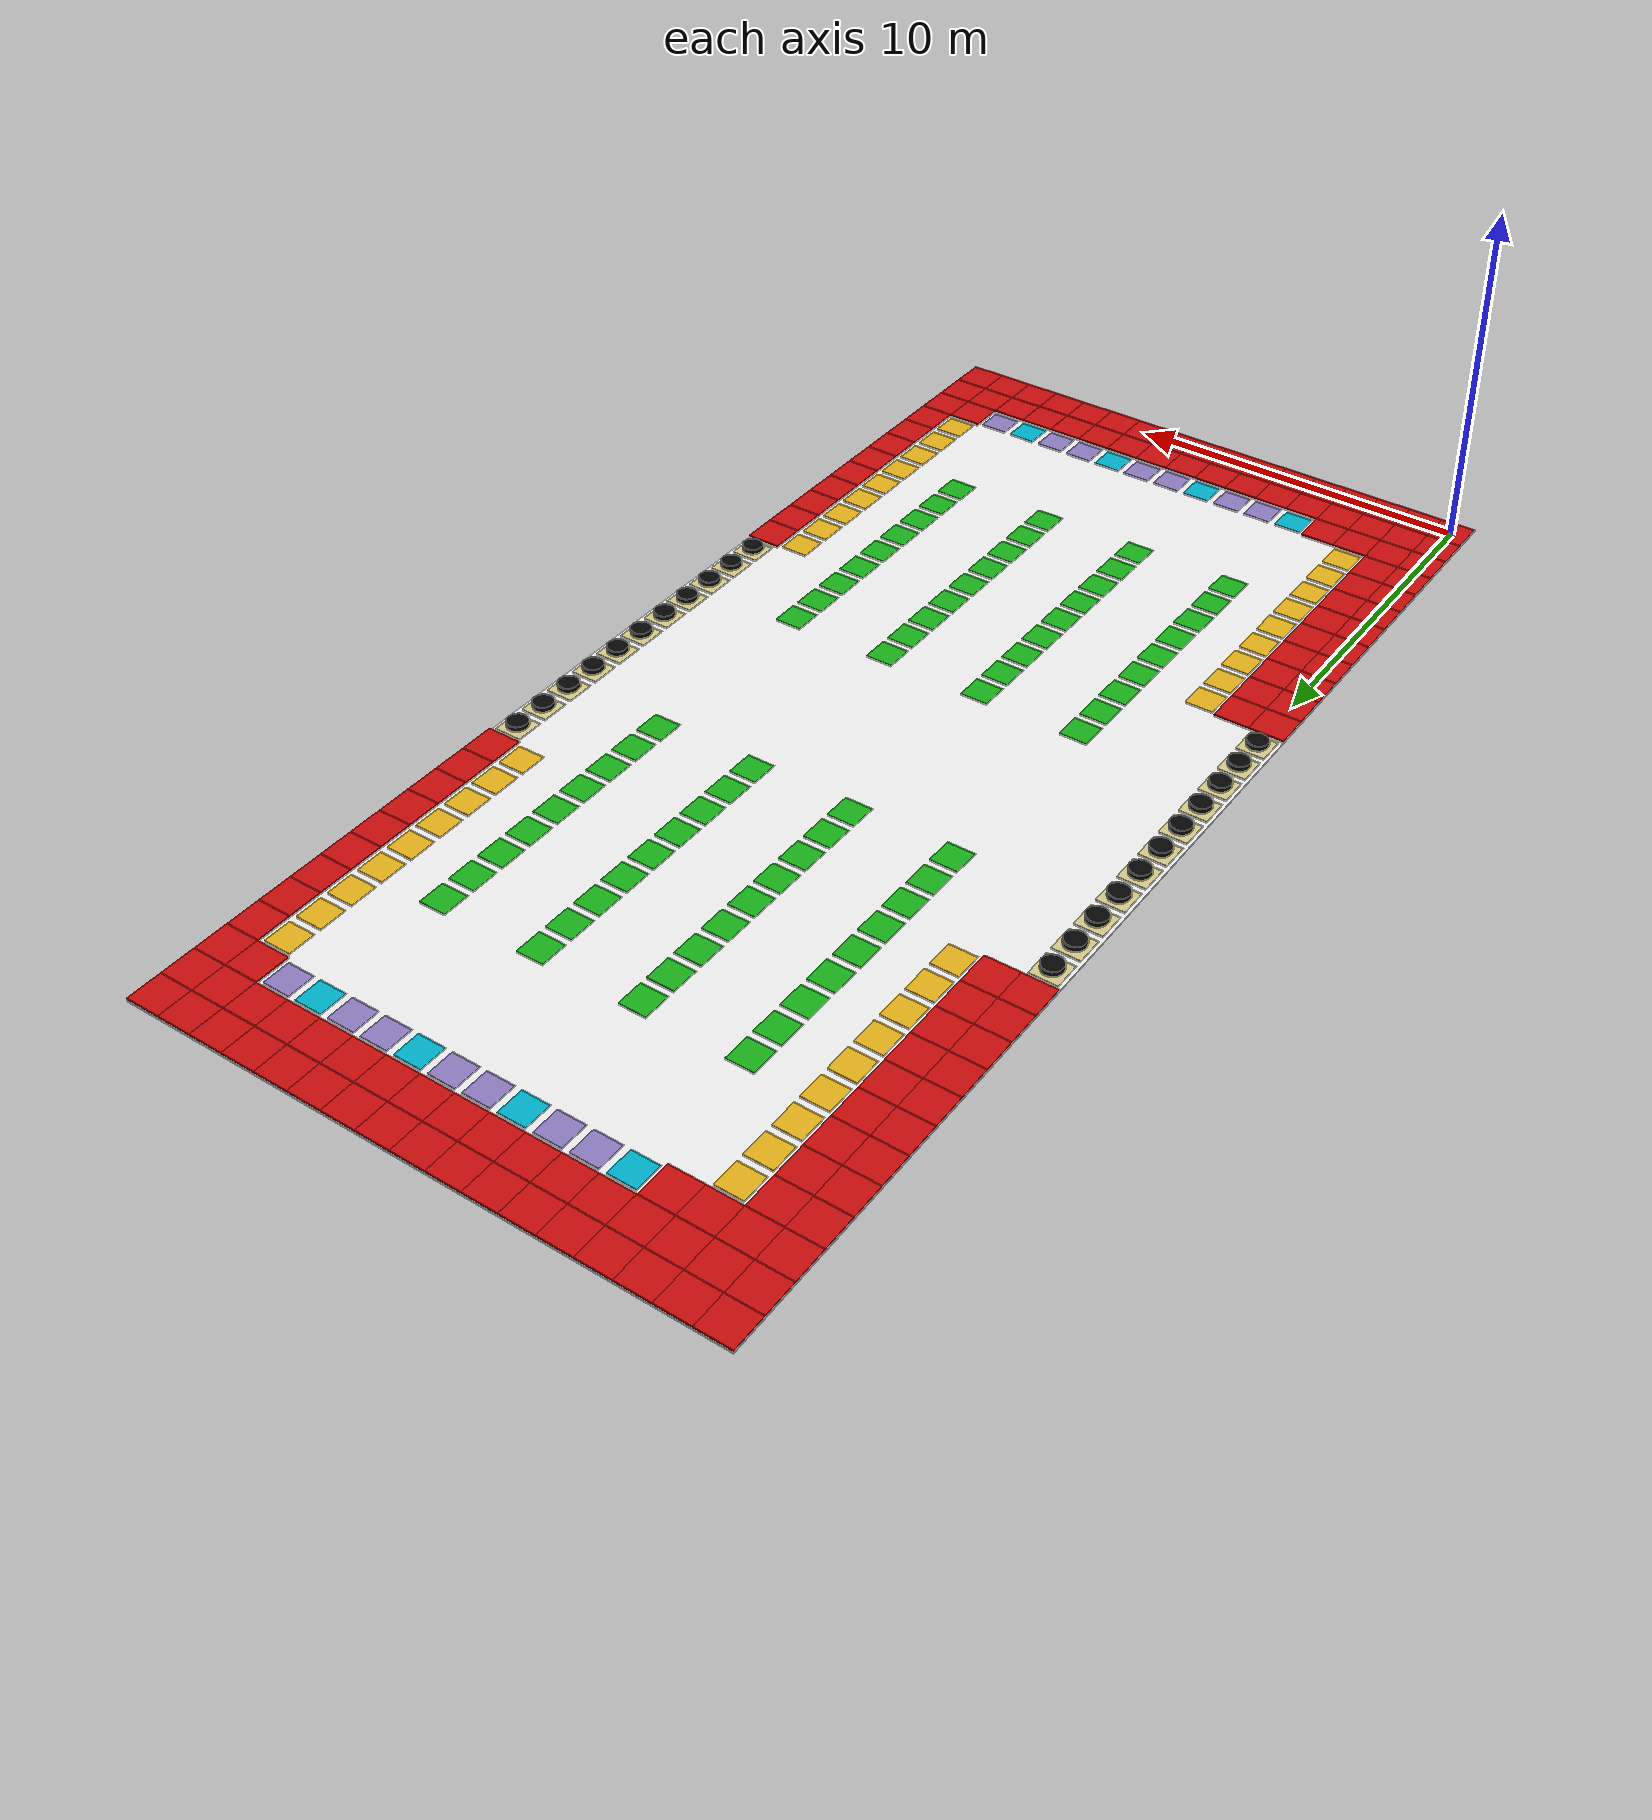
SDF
<?xml version="1.0"?>
<sdf version="1.10">
  <world name="warehouse_grid">

    <plugin
      filename="gz-sim-physics-system"
      name="gz::sim::systems::Physics">
    </plugin>

    <plugin
      filename="gz-sim-user-commands-system"
      name="gz::sim::systems::UserCommands">
    </plugin>

    <plugin
      filename="gz-sim-scene-broadcaster-system"
      name="gz::sim::systems::SceneBroadcaster">
    </plugin>

    <scene>
      <ambient>0.8 0.8 0.8 1</ambient>
      <background>0.6 0.6 0.6 1</background>
      <shadows>false</shadows>
    </scene>

    <light type="directional" name="sun">
      <pose>0 0 20 0 0 0</pose>
      <direction>0 0 -1</direction>
      <diffuse>1 1 1 1</diffuse>
      <specular>0.2 0.2 0.2 1</specular>
      <cast_shadows>false</cast_shadows>
    </light>

    <model name="warehouse_floor">
      <static>true</static>

      <pose>
        8.0
        17.0
        0.0
        0 0 0
      </pose>

      <link name="floor_link">

        <visual name="floor_visual">
          <geometry>
            <box>
              <size>
                17.0
                35.0
                0.02
              </size>
            </box>
          </geometry>

          <material>
            <ambient>0.95 0.95 0.95 1</ambient>
            <diffuse>0.95 0.95 0.95 1</diffuse>
          </material>
        </visual>

      </link>
    </model>

    <model name="blocked_0000">
      <static>true</static>

      <pose>
        0.0
        0.0
        0.045
        0 0 0
      </pose>

      <link name="link">

        <visual name="visual">
          <geometry>
            <box>
              <size>
                1.0
                1.0
                0.05
              </size>
            </box>
          </geometry>

          <material>
            <ambient>0.8 0.05 0.05 1</ambient>
            <diffuse>0.8 0.05 0.05 1</diffuse>
          </material>
        </visual>

      </link>
    </model>

    <model name="blocked_0001">
      <static>true</static>

      <pose>
        0.0
        1.0
        0.045
        0 0 0
      </pose>

      <link name="link">

        <visual name="visual">
          <geometry>
            <box>
              <size>
                1.0
                1.0
                0.05
              </size>
            </box>
          </geometry>

          <material>
            <ambient>0.8 0.05 0.05 1</ambient>
            <diffuse>0.8 0.05 0.05 1</diffuse>
          </material>
        </visual>

      </link>
    </model>

    <model name="blocked_0002">
      <static>true</static>

      <pose>
        0.0
        2.0
        0.045
        0 0 0
      </pose>

      <link name="link">

        <visual name="visual">
          <geometry>
            <box>
              <size>
                1.0
                1.0
                0.05
              </size>
            </box>
          </geometry>

          <material>
            <ambient>0.8 0.05 0.05 1</ambient>
            <diffuse>0.8 0.05 0.05 1</diffuse>
          </material>
        </visual>

      </link>
    </model>

    <model name="blocked_0003">
      <static>true</static>

      <pose>
        0.0
        3.0
        0.045
        0 0 0
      </pose>

      <link name="link">

        <visual name="visual">
          <geometry>
            <box>
              <size>
                1.0
                1.0
                0.05
              </size>
            </box>
          </geometry>

          <material>
            <ambient>0.8 0.05 0.05 1</ambient>
            <diffuse>0.8 0.05 0.05 1</diffuse>
          </material>
        </visual>

      </link>
    </model>

    <model name="blocked_0004">
      <static>true</static>

      <pose>
        0.0
        4.0
        0.045
        0 0 0
      </pose>

      <link name="link">

        <visual name="visual">
          <geometry>
            <box>
              <size>
                1.0
                1.0
                0.05
              </size>
            </box>
          </geometry>

          <material>
            <ambient>0.8 0.05 0.05 1</ambient>
            <diffuse>0.8 0.05 0.05 1</diffuse>
          </material>
        </visual>

      </link>
    </model>

    <model name="blocked_0005">
      <static>true</static>

      <pose>
        0.0
        5.0
        0.045
        0 0 0
      </pose>

      <link name="link">

        <visual name="visual">
          <geometry>
            <box>
              <size>
                1.0
                1.0
                0.05
              </size>
            </box>
          </geometry>

          <material>
            <ambient>0.8 0.05 0.05 1</ambient>
            <diffuse>0.8 0.05 0.05 1</diffuse>
          </material>
        </visual>

      </link>
    </model>

    <model name="blocked_0006">
      <static>true</static>

      <pose>
        0.0
        6.0
        0.045
        0 0 0
      </pose>

      <link name="link">

        <visual name="visual">
          <geometry>
            <box>
              <size>
                1.0
                1.0
                0.05
              </size>
            </box>
          </geometry>

          <material>
            <ambient>0.8 0.05 0.05 1</ambient>
            <diffuse>0.8 0.05 0.05 1</diffuse>
          </material>
        </visual>

      </link>
    </model>

    <model name="blocked_0007">
      <static>true</static>

      <pose>
        0.0
        7.0
        0.045
        0 0 0
      </pose>

      <link name="link">

        <visual name="visual">
          <geometry>
            <box>
              <size>
                1.0
                1.0
                0.05
              </size>
            </box>
          </geometry>

          <material>
            <ambient>0.8 0.05 0.05 1</ambient>
            <diffuse>0.8 0.05 0.05 1</diffuse>
          </material>
        </visual>

      </link>
    </model>

    <model name="blocked_0008">
      <static>true</static>

      <pose>
        0.0
        8.0
        0.045
        0 0 0
      </pose>

      <link name="link">

        <visual name="visual">
          <geometry>
            <box>
              <size>
                1.0
                1.0
                0.05
              </size>
            </box>
          </geometry>

          <material>
            <ambient>0.8 0.05 0.05 1</ambient>
            <diffuse>0.8 0.05 0.05 1</diffuse>
          </material>
        </visual>

      </link>
    </model>

    <model name="blocked_0009">
      <static>true</static>

      <pose>
        0.0
        9.0
        0.045
        0 0 0
      </pose>

      <link name="link">

        <visual name="visual">
          <geometry>
            <box>
              <size>
                1.0
                1.0
                0.05
              </size>
            </box>
          </geometry>

          <material>
            <ambient>0.8 0.05 0.05 1</ambient>
            <diffuse>0.8 0.05 0.05 1</diffuse>
          </material>
        </visual>

      </link>
    </model>

    <model name="blocked_0010">
      <static>true</static>

      <pose>
        0.0
        10.0
        0.045
        0 0 0
      </pose>

      <link name="link">

        <visual name="visual">
          <geometry>
            <box>
              <size>
                1.0
                1.0
                0.05
              </size>
            </box>
          </geometry>

          <material>
            <ambient>0.8 0.05 0.05 1</ambient>
            <diffuse>0.8 0.05 0.05 1</diffuse>
          </material>
        </visual>

      </link>
    </model>

    <model name="blocked_0011">
      <static>true</static>

      <pose>
        0.0
        11.0
        0.045
        0 0 0
      </pose>

      <link name="link">

        <visual name="visual">
          <geometry>
            <box>
              <size>
                1.0
                1.0
                0.05
              </size>
            </box>
          </geometry>

          <material>
            <ambient>0.8 0.05 0.05 1</ambient>
            <diffuse>0.8 0.05 0.05 1</diffuse>
          </material>
        </visual>

      </link>
    </model>

    <model name="blocked_0012">
      <static>true</static>

      <pose>
        0.0
        23.0
        0.045
        0 0 0
      </pose>

      <link name="link">

        <visual name="visual">
          <geometry>
            <box>
              <size>
                1.0
                1.0
                0.05
              </size>
            </box>
          </geometry>

          <material>
            <ambient>0.8 0.05 0.05 1</ambient>
            <diffuse>0.8 0.05 0.05 1</diffuse>
          </material>
        </visual>

      </link>
    </model>

    <model name="blocked_0013">
      <static>true</static>

      <pose>
        0.0
        24.0
        0.045
        0 0 0
      </pose>

      <link name="link">

        <visual name="visual">
          <geometry>
            <box>
              <size>
                1.0
                1.0
                0.05
              </size>
            </box>
          </geometry>

          <material>
            <ambient>0.8 0.05 0.05 1</ambient>
            <diffuse>0.8 0.05 0.05 1</diffuse>
          </material>
        </visual>

      </link>
    </model>

    <model name="blocked_0014">
      <static>true</static>

      <pose>
        0.0
        25.0
        0.045
        0 0 0
      </pose>

      <link name="link">

        <visual name="visual">
          <geometry>
            <box>
              <size>
                1.0
                1.0
                0.05
              </size>
            </box>
          </geometry>

          <material>
            <ambient>0.8 0.05 0.05 1</ambient>
            <diffuse>0.8 0.05 0.05 1</diffuse>
          </material>
        </visual>

      </link>
    </model>

    <model name="blocked_0015">
      <static>true</static>

      <pose>
        0.0
        26.0
        0.045
        0 0 0
      </pose>

      <link name="link">

        <visual name="visual">
          <geometry>
            <box>
              <size>
                1.0
                1.0
                0.05
              </size>
            </box>
          </geometry>

          <material>
            <ambient>0.8 0.05 0.05 1</ambient>
            <diffuse>0.8 0.05 0.05 1</diffuse>
          </material>
        </visual>

      </link>
    </model>

    <model name="blocked_0016">
      <static>true</static>

      <pose>
        0.0
        27.0
        0.045
        0 0 0
      </pose>

      <link name="link">

        <visual name="visual">
          <geometry>
            <box>
              <size>
                1.0
                1.0
                0.05
              </size>
            </box>
          </geometry>

          <material>
            <ambient>0.8 0.05 0.05 1</ambient>
            <diffuse>0.8 0.05 0.05 1</diffuse>
          </material>
        </visual>

      </link>
    </model>

    <model name="blocked_0017">
      <static>true</static>

      <pose>
        0.0
        28.0
        0.045
        0 0 0
      </pose>

      <link name="link">

        <visual name="visual">
          <geometry>
            <box>
              <size>
                1.0
                1.0
                0.05
              </size>
            </box>
          </geometry>

          <material>
            <ambient>0.8 0.05 0.05 1</ambient>
            <diffuse>0.8 0.05 0.05 1</diffuse>
          </material>
        </visual>

      </link>
    </model>

    <model name="blocked_0018">
      <static>true</static>

      <pose>
        0.0
        29.0
        0.045
        0 0 0
      </pose>

      <link name="link">

        <visual name="visual">
          <geometry>
            <box>
              <size>
                1.0
                1.0
                0.05
              </size>
            </box>
          </geometry>

          <material>
            <ambient>0.8 0.05 0.05 1</ambient>
            <diffuse>0.8 0.05 0.05 1</diffuse>
          </material>
        </visual>

      </link>
    </model>

    <model name="blocked_0019">
      <static>true</static>

      <pose>
        0.0
        30.0
        0.045
        0 0 0
      </pose>

      <link name="link">

        <visual name="visual">
          <geometry>
            <box>
              <size>
                1.0
                1.0
                0.05
              </size>
            </box>
          </geometry>

          <material>
            <ambient>0.8 0.05 0.05 1</ambient>
            <diffuse>0.8 0.05 0.05 1</diffuse>
          </material>
        </visual>

      </link>
    </model>

    <model name="blocked_0020">
      <static>true</static>

      <pose>
        0.0
        31.0
        0.045
        0 0 0
      </pose>

      <link name="link">

        <visual name="visual">
          <geometry>
            <box>
              <size>
                1.0
                1.0
                0.05
              </size>
            </box>
          </geometry>

          <material>
            <ambient>0.8 0.05 0.05 1</ambient>
            <diffuse>0.8 0.05 0.05 1</diffuse>
          </material>
        </visual>

      </link>
    </model>

    <model name="blocked_0021">
      <static>true</static>

      <pose>
        0.0
        32.0
        0.045
        0 0 0
      </pose>

      <link name="link">

        <visual name="visual">
          <geometry>
            <box>
              <size>
                1.0
                1.0
                0.05
              </size>
            </box>
          </geometry>

          <material>
            <ambient>0.8 0.05 0.05 1</ambient>
            <diffuse>0.8 0.05 0.05 1</diffuse>
          </material>
        </visual>

      </link>
    </model>

    <model name="blocked_0022">
      <static>true</static>

      <pose>
        0.0
        33.0
        0.045
        0 0 0
      </pose>

      <link name="link">

        <visual name="visual">
          <geometry>
            <box>
              <size>
                1.0
                1.0
                0.05
              </size>
            </box>
          </geometry>

          <material>
            <ambient>0.8 0.05 0.05 1</ambient>
            <diffuse>0.8 0.05 0.05 1</diffuse>
          </material>
        </visual>

      </link>
    </model>

    <model name="blocked_0023">
      <static>true</static>

      <pose>
        0.0
        34.0
        0.045
        0 0 0
      </pose>

      <link name="link">

        <visual name="visual">
          <geometry>
            <box>
              <size>
                1.0
                1.0
                0.05
              </size>
            </box>
          </geometry>

          <material>
            <ambient>0.8 0.05 0.05 1</ambient>
            <diffuse>0.8 0.05 0.05 1</diffuse>
          </material>
        </visual>

      </link>
    </model>

    <model name="blocked_0024">
      <static>true</static>

      <pose>
        1.0
        0.0
        0.045
        0 0 0
      </pose>

      <link name="link">

        <visual name="visual">
          <geometry>
            <box>
              <size>
                1.0
                1.0
                0.05
              </size>
            </box>
          </geometry>

          <material>
            <ambient>0.8 0.05 0.05 1</ambient>
            <diffuse>0.8 0.05 0.05 1</diffuse>
          </material>
        </visual>

      </link>
    </model>

    <model name="blocked_0025">
      <static>true</static>

      <pose>
        1.0
        1.0
        0.045
        0 0 0
      </pose>

      <link name="link">

        <visual name="visual">
          <geometry>
            <box>
              <size>
                1.0
                1.0
                0.05
              </size>
            </box>
          </geometry>

          <material>
            <ambient>0.8 0.05 0.05 1</ambient>
            <diffuse>0.8 0.05 0.05 1</diffuse>
          </material>
        </visual>

      </link>
    </model>

    <model name="blocked_0026">
      <static>true</static>

      <pose>
        1.0
        2.0
        0.045
        0 0 0
      </pose>

      <link name="link">

        <visual name="visual">
          <geometry>
            <box>
              <size>
                1.0
                1.0
                0.05
              </size>
            </box>
          </geometry>

          <material>
            <ambient>0.8 0.05 0.05 1</ambient>
            <diffuse>0.8 0.05 0.05 1</diffuse>
          </material>
        </visual>

      </link>
    </model>

    <model name="blocked_0027">
      <static>true</static>

      <pose>
        1.0
        3.0
        0.045
        0 0 0
      </pose>

      <link name="link">

        <visual name="visual">
          <geometry>
            <box>
              <size>
                1.0
                1.0
                0.05
              </size>
            </box>
          </geometry>

          <material>
            <ambient>0.8 0.05 0.05 1</ambient>
            <diffuse>0.8 0.05 0.05 1</diffuse>
          </material>
        </visual>

      </link>
    </model>

    <model name="blocked_0028">
      <static>true</static>

      <pose>
        1.0
        4.0
        0.045
        0 0 0
      </pose>

      <link name="link">

        <visual name="visual">
          <geometry>
            <box>
              <size>
                1.0
                1.0
                0.05
              </size>
            </box>
          </geometry>

          <material>
            <ambient>0.8 0.05 0.05 1</ambient>
            <diffuse>0.8 0.05 0.05 1</diffuse>
          </material>
        </visual>

      </link>
    </model>

    <model name="blocked_0029">
      <static>true</static>

      <pose>
        1.0
        5.0
        0.045
        0 0 0
      </pose>

      <link name="link">

        <visual name="visual">
          <geometry>
            <box>
              <size>
                1.0
                1.0
                0.05
              </size>
            </box>
          </geometry>

          <material>
            <ambient>0.8 0.05 0.05 1</ambient>
            <diffuse>0.8 0.05 0.05 1</diffuse>
          </material>
        </visual>

      </link>
    </model>

    <model name="blocked_0030">
      <static>true</static>

      <pose>
        1.0
        6.0
        0.045
        0 0 0
      </pose>

      <link name="link">

        <visual name="visual">
          <geometry>
            <box>
              <size>
                1.0
                1.0
                0.05
              </size>
            </box>
          </geometry>

          <material>
            <ambient>0.8 0.05 0.05 1</ambient>
            <diffuse>0.8 0.05 0.05 1</diffuse>
          </material>
        </visual>

      </link>
    </model>

    <model name="blocked_0031">
      <static>true</static>

      <pose>
        1.0
        7.0
        0.045
        0 0 0
      </pose>

      <link name="link">

        <visual name="visual">
          <geometry>
            <box>
              <size>
                1.0
                1.0
                0.05
              </size>
            </box>
          </geometry>

          <material>
            <ambient>0.8 0.05 0.05 1</ambient>
            <diffuse>0.8 0.05 0.05 1</diffuse>
          </material>
        </visual>

      </link>
    </model>

    <model name="blocked_0032">
      <static>true</static>

      <pose>
        1.0
        8.0
        0.045
        0 0 0
      </pose>

      <link name="link">

        <visual name="visual">
          <geometry>
            <box>
              <size>
                1.0
                1.0
                0.05
              </size>
            </box>
          </geometry>

          <material>
            <ambient>0.8 0.05 0.05 1</ambient>
            <diffuse>0.8 0.05 0.05 1</diffuse>
          </material>
        </visual>

      </link>
    </model>

    <model name="blocked_0033">
      <static>true</static>

      <pose>
        1.0
        9.0
        0.045
        0 0 0
      </pose>

      <link name="link">

        <visual name="visual">
          <geometry>
            <box>
              <size>
                1.0
                1.0
                0.05
              </size>
            </box>
          </geometry>

          <material>
            <ambient>0.8 0.05 0.05 1</ambient>
            <diffuse>0.8 0.05 0.05 1</diffuse>
          </material>
        </visual>

      </link>
    </model>

    <model name="blocked_0034">
      <static>true</static>

      <pose>
        1.0
        10.0
        0.045
        0 0 0
      </pose>

      <link name="link">

        <visual name="visual">
          <geometry>
            <box>
              <size>
                1.0
                1.0
                0.05
              </size>
            </box>
          </geometry>

          <material>
            <ambient>0.8 0.05 0.05 1</ambient>
            <diffuse>0.8 0.05 0.05 1</diffuse>
          </material>
        </visual>

      </link>
    </model>

    <model name="blocked_0035">
      <static>true</static>

      <pose>
        1.0
        11.0
        0.045
        0 0 0
      </pose>

      <link name="link">

        <visual name="visual">
          <geometry>
            <box>
              <size>
                1.0
                1.0
                0.05
              </size>
            </box>
          </geometry>

          <material>
            <ambient>0.8 0.05 0.05 1</ambient>
            <diffuse>0.8 0.05 0.05 1</diffuse>
          </material>
        </visual>

      </link>
    </model>

    <model name="blocked_0036">
      <static>true</static>

      <pose>
        1.0
        23.0
        0.045
        0 0 0
      </pose>

      <link name="link">

        <visual name="visual">
          <geometry>
            <box>
              <size>
                1.0
                1.0
                0.05
              </size>
            </box>
          </geometry>

          <material>
            <ambient>0.8 0.05 0.05 1</ambient>
            <diffuse>0.8 0.05 0.05 1</diffuse>
          </material>
        </visual>

      </link>
    </model>

    <model name="blocked_0037">
      <static>true</static>

      <pose>
        1.0
        24.0
        0.045
        0 0 0
      </pose>

      <link name="link">

        <visual name="visual">
          <geometry>
            <box>
              <size>
                1.0
                1.0
                0.05
              </size>
            </box>
          </geometry>

          <material>
            <ambient>0.8 0.05 0.05 1</ambient>
            <diffuse>0.8 0.05 0.05 1</diffuse>
          </material>
        </visual>

      </link>
    </model>

    <model name="blocked_0038">
      <static>true</static>

      <pose>
        1.0
        25.0
        0.045
        0 0 0
      </pose>

      <link name="link">

        <visual name="visual">
          <geometry>
            <box>
              <size>
                1.0
                1.0
                0.05
              </size>
            </box>
          </geometry>

          <material>
            <ambient>0.8 0.05 0.05 1</ambient>
            <diffuse>0.8 0.05 0.05 1</diffuse>
          </material>
        </visual>

      </link>
    </model>

    <model name="blocked_0039">
      <static>true</static>

      <pose>
        1.0
        26.0
        0.045
        0 0 0
      </pose>

      <link name="link">

        <visual name="visual">
          <geometry>
            <box>
              <size>
                1.0
                1.0
                0.05
              </size>
            </box>
          </geometry>

          <material>
            <ambient>0.8 0.05 0.05 1</ambient>
            <diffuse>0.8 0.05 0.05 1</diffuse>
          </material>
        </visual>

      </link>
    </model>

    <model name="blocked_0040">
      <static>true</static>

      <pose>
        1.0
        27.0
        0.045
        0 0 0
      </pose>

      <link name="link">

        <visual name="visual">
          <geometry>
            <box>
              <size>
                1.0
                1.0
                0.05
              </size>
            </box>
          </geometry>

          <material>
            <ambient>0.8 0.05 0.05 1</ambient>
            <diffuse>0.8 0.05 0.05 1</diffuse>
          </material>
        </visual>

      </link>
    </model>

    <model name="blocked_0041">
      <static>true</static>

      <pose>
        1.0
        28.0
        0.045
        0 0 0
      </pose>

      <link name="link">

        <visual name="visual">
          <geometry>
            <box>
              <size>
                1.0
                1.0
                0.05
              </size>
            </box>
          </geometry>

          <material>
            <ambient>0.8 0.05 0.05 1</ambient>
            <diffuse>0.8 0.05 0.05 1</diffuse>
          </material>
        </visual>

      </link>
    </model>

    <model name="blocked_0042">
      <static>true</static>

      <pose>
        1.0
        29.0
        0.045
        0 0 0
      </pose>

      <link name="link">

        <visual name="visual">
          <geometry>
            <box>
              <size>
                1.0
                1.0
                0.05
              </size>
            </box>
          </geometry>

          <material>
            <ambient>0.8 0.05 0.05 1</ambient>
            <diffuse>0.8 0.05 0.05 1</diffuse>
          </material>
        </visual>

      </link>
    </model>

    <model name="blocked_0043">
      <static>true</static>

      <pose>
        1.0
        30.0
        0.045
        0 0 0
      </pose>

      <link name="link">

        <visual name="visual">
          <geometry>
            <box>
              <size>
                1.0
                1.0
                0.05
              </size>
            </box>
          </geometry>

          <material>
            <ambient>0.8 0.05 0.05 1</ambient>
            <diffuse>0.8 0.05 0.05 1</diffuse>
          </material>
        </visual>

      </link>
    </model>

    <model name="blocked_0044">
      <static>true</static>

      <pose>
        1.0
        31.0
        0.045
        0 0 0
      </pose>

      <link name="link">

        <visual name="visual">
          <geometry>
            <box>
              <size>
                1.0
                1.0
                0.05
              </size>
            </box>
          </geometry>

          <material>
            <ambient>0.8 0.05 0.05 1</ambient>
            <diffuse>0.8 0.05 0.05 1</diffuse>
          </material>
        </visual>

      </link>
    </model>

    <model name="blocked_0045">
      <static>true</static>

      <pose>
        1.0
        32.0
        0.045
        0 0 0
      </pose>

      <link name="link">

        <visual name="visual">
          <geometry>
            <box>
              <size>
                1.0
                1.0
                0.05
              </size>
            </box>
          </geometry>

          <material>
            <ambient>0.8 0.05 0.05 1</ambient>
            <diffuse>0.8 0.05 0.05 1</diffuse>
          </material>
        </visual>

      </link>
    </model>

    <model name="blocked_0046">
      <static>true</static>

      <pose>
        1.0
        33.0
        0.045
        0 0 0
      </pose>

      <link name="link">

        <visual name="visual">
          <geometry>
            <box>
              <size>
                1.0
                1.0
                0.05
              </size>
            </box>
          </geometry>

          <material>
            <ambient>0.8 0.05 0.05 1</ambient>
            <diffuse>0.8 0.05 0.05 1</diffuse>
          </material>
        </visual>

      </link>
    </model>

    <model name="blocked_0047">
      <static>true</static>

      <pose>
        1.0
        34.0
        0.045
        0 0 0
      </pose>

      <link name="link">

        <visual name="visual">
          <geometry>
            <box>
              <size>
                1.0
                1.0
                0.05
              </size>
            </box>
          </geometry>

          <material>
            <ambient>0.8 0.05 0.05 1</ambient>
            <diffuse>0.8 0.05 0.05 1</diffuse>
          </material>
        </visual>

      </link>
    </model>

    <model name="blocked_0048">
      <static>true</static>

      <pose>
        2.0
        0.0
        0.045
        0 0 0
      </pose>

      <link name="link">

        <visual name="visual">
          <geometry>
            <box>
              <size>
                1.0
                1.0
                0.05
              </size>
            </box>
          </geometry>

          <material>
            <ambient>0.8 0.05 0.05 1</ambient>
            <diffuse>0.8 0.05 0.05 1</diffuse>
          </material>
        </visual>

      </link>
    </model>

    <model name="blocked_0049">
      <static>true</static>

      <pose>
        2.0
        1.0
        0.045
        0 0 0
      </pose>

      <link name="link">

        <visual name="visual">
          <geometry>
            <box>
              <size>
                1.0
                1.0
                0.05
              </size>
            </box>
          </geometry>

          <material>
            <ambient>0.8 0.05 0.05 1</ambient>
            <diffuse>0.8 0.05 0.05 1</diffuse>
          </material>
        </visual>

      </link>
    </model>

    <model name="blocked_0050">
      <static>true</static>

      <pose>
        2.0
        2.0
        0.045
        0 0 0
      </pose>

      <link name="link">

        <visual name="visual">
          <geometry>
            <box>
              <size>
                1.0
                1.0
                0.05
              </size>
            </box>
          </geometry>

          <material>
            <ambient>0.8 0.05 0.05 1</ambient>
            <diffuse>0.8 0.05 0.05 1</diffuse>
          </material>
        </visual>

      </link>
    </model>

    <model name="blocked_0051">
      <static>true</static>

      <pose>
        2.0
        32.0
        0.045
        0 0 0
      </pose>

      <link name="link">

        <visual name="visual">
          <geometry>
            <box>
              <size>
                1.0
                1.0
                0.05
              </size>
            </box>
          </geometry>

          <material>
            <ambient>0.8 0.05 0.05 1</ambient>
            <diffuse>0.8 0.05 0.05 1</diffuse>
          </material>
        </visual>

      </link>
    </model>

    <model name="blocked_0052">
      <static>true</static>

      <pose>
        2.0
        33.0
        0.045
        0 0 0
      </pose>

      <link name="link">

        <visual name="visual">
          <geometry>
            <box>
              <size>
                1.0
                1.0
                0.05
              </size>
            </box>
          </geometry>

          <material>
            <ambient>0.8 0.05 0.05 1</ambient>
            <diffuse>0.8 0.05 0.05 1</diffuse>
          </material>
        </visual>

      </link>
    </model>

    <model name="blocked_0053">
      <static>true</static>

      <pose>
        2.0
        34.0
        0.045
        0 0 0
      </pose>

      <link name="link">

        <visual name="visual">
          <geometry>
            <box>
              <size>
                1.0
                1.0
                0.05
              </size>
            </box>
          </geometry>

          <material>
            <ambient>0.8 0.05 0.05 1</ambient>
            <diffuse>0.8 0.05 0.05 1</diffuse>
          </material>
        </visual>

      </link>
    </model>

    <model name="blocked_0054">
      <static>true</static>

      <pose>
        3.0
        0.0
        0.045
        0 0 0
      </pose>

      <link name="link">

        <visual name="visual">
          <geometry>
            <box>
              <size>
                1.0
                1.0
                0.05
              </size>
            </box>
          </geometry>

          <material>
            <ambient>0.8 0.05 0.05 1</ambient>
            <diffuse>0.8 0.05 0.05 1</diffuse>
          </material>
        </visual>

      </link>
    </model>

    <model name="blocked_0055">
      <static>true</static>

      <pose>
        3.0
        1.0
        0.045
        0 0 0
      </pose>

      <link name="link">

        <visual name="visual">
          <geometry>
            <box>
              <size>
                1.0
                1.0
                0.05
              </size>
            </box>
          </geometry>

          <material>
            <ambient>0.8 0.05 0.05 1</ambient>
            <diffuse>0.8 0.05 0.05 1</diffuse>
          </material>
        </visual>

      </link>
    </model>

    <model name="blocked_0056">
      <static>true</static>

      <pose>
        3.0
        2.0
        0.045
        0 0 0
      </pose>

      <link name="link">

        <visual name="visual">
          <geometry>
            <box>
              <size>
                1.0
                1.0
                0.05
              </size>
            </box>
          </geometry>

          <material>
            <ambient>0.8 0.05 0.05 1</ambient>
            <diffuse>0.8 0.05 0.05 1</diffuse>
          </material>
        </visual>

      </link>
    </model>

    <model name="blocked_0057">
      <static>true</static>

      <pose>
        3.0
        32.0
        0.045
        0 0 0
      </pose>

      <link name="link">

        <visual name="visual">
          <geometry>
            <box>
              <size>
                1.0
                1.0
                0.05
              </size>
            </box>
          </geometry>

          <material>
            <ambient>0.8 0.05 0.05 1</ambient>
            <diffuse>0.8 0.05 0.05 1</diffuse>
          </material>
        </visual>

      </link>
    </model>

    <model name="blocked_0058">
      <static>true</static>

      <pose>
        3.0
        33.0
        0.045
        0 0 0
      </pose>

      <link name="link">

        <visual name="visual">
          <geometry>
            <box>
              <size>
                1.0
                1.0
                0.05
              </size>
            </box>
          </geometry>

          <material>
            <ambient>0.8 0.05 0.05 1</ambient>
            <diffuse>0.8 0.05 0.05 1</diffuse>
          </material>
        </visual>

      </link>
    </model>

    <model name="blocked_0059">
      <static>true</static>

      <pose>
        3.0
        34.0
        0.045
        0 0 0
      </pose>

      <link name="link">

        <visual name="visual">
          <geometry>
            <box>
              <size>
                1.0
                1.0
                0.05
              </size>
            </box>
          </geometry>

          <material>
            <ambient>0.8 0.05 0.05 1</ambient>
            <diffuse>0.8 0.05 0.05 1</diffuse>
          </material>
        </visual>

      </link>
    </model>

    <model name="blocked_0060">
      <static>true</static>

      <pose>
        4.0
        0.0
        0.045
        0 0 0
      </pose>

      <link name="link">

        <visual name="visual">
          <geometry>
            <box>
              <size>
                1.0
                1.0
                0.05
              </size>
            </box>
          </geometry>

          <material>
            <ambient>0.8 0.05 0.05 1</ambient>
            <diffuse>0.8 0.05 0.05 1</diffuse>
          </material>
        </visual>

      </link>
    </model>

    <model name="blocked_0061">
      <static>true</static>

      <pose>
        4.0
        1.0
        0.045
        0 0 0
      </pose>

      <link name="link">

        <visual name="visual">
          <geometry>
            <box>
              <size>
                1.0
                1.0
                0.05
              </size>
            </box>
          </geometry>

          <material>
            <ambient>0.8 0.05 0.05 1</ambient>
            <diffuse>0.8 0.05 0.05 1</diffuse>
          </material>
        </visual>

      </link>
    </model>

    <model name="blocked_0062">
      <static>true</static>

      <pose>
        4.0
        33.0
        0.045
        0 0 0
      </pose>

      <link name="link">

        <visual name="visual">
          <geometry>
            <box>
              <size>
                1.0
                1.0
                0.05
              </size>
            </box>
          </geometry>

          <material>
            <ambient>0.8 0.05 0.05 1</ambient>
            <diffuse>0.8 0.05 0.05 1</diffuse>
          </material>
        </visual>

      </link>
    </model>

    <model name="blocked_0063">
      <static>true</static>

      <pose>
        4.0
        34.0
        0.045
        0 0 0
      </pose>

      <link name="link">

        <visual name="visual">
          <geometry>
            <box>
              <size>
                1.0
                1.0
                0.05
              </size>
            </box>
          </geometry>

          <material>
            <ambient>0.8 0.05 0.05 1</ambient>
            <diffuse>0.8 0.05 0.05 1</diffuse>
          </material>
        </visual>

      </link>
    </model>

    <model name="blocked_0064">
      <static>true</static>

      <pose>
        5.0
        0.0
        0.045
        0 0 0
      </pose>

      <link name="link">

        <visual name="visual">
          <geometry>
            <box>
              <size>
                1.0
                1.0
                0.05
              </size>
            </box>
          </geometry>

          <material>
            <ambient>0.8 0.05 0.05 1</ambient>
            <diffuse>0.8 0.05 0.05 1</diffuse>
          </material>
        </visual>

      </link>
    </model>

    <model name="blocked_0065">
      <static>true</static>

      <pose>
        5.0
        1.0
        0.045
        0 0 0
      </pose>

      <link name="link">

        <visual name="visual">
          <geometry>
            <box>
              <size>
                1.0
                1.0
                0.05
              </size>
            </box>
          </geometry>

          <material>
            <ambient>0.8 0.05 0.05 1</ambient>
            <diffuse>0.8 0.05 0.05 1</diffuse>
          </material>
        </visual>

      </link>
    </model>

    <model name="blocked_0066">
      <static>true</static>

      <pose>
        5.0
        33.0
        0.045
        0 0 0
      </pose>

      <link name="link">

        <visual name="visual">
          <geometry>
            <box>
              <size>
                1.0
                1.0
                0.05
              </size>
            </box>
          </geometry>

          <material>
            <ambient>0.8 0.05 0.05 1</ambient>
            <diffuse>0.8 0.05 0.05 1</diffuse>
          </material>
        </visual>

      </link>
    </model>

    <model name="blocked_0067">
      <static>true</static>

      <pose>
        5.0
        34.0
        0.045
        0 0 0
      </pose>

      <link name="link">

        <visual name="visual">
          <geometry>
            <box>
              <size>
                1.0
                1.0
                0.05
              </size>
            </box>
          </geometry>

          <material>
            <ambient>0.8 0.05 0.05 1</ambient>
            <diffuse>0.8 0.05 0.05 1</diffuse>
          </material>
        </visual>

      </link>
    </model>

    <model name="blocked_0068">
      <static>true</static>

      <pose>
        6.0
        0.0
        0.045
        0 0 0
      </pose>

      <link name="link">

        <visual name="visual">
          <geometry>
            <box>
              <size>
                1.0
                1.0
                0.05
              </size>
            </box>
          </geometry>

          <material>
            <ambient>0.8 0.05 0.05 1</ambient>
            <diffuse>0.8 0.05 0.05 1</diffuse>
          </material>
        </visual>

      </link>
    </model>

    <model name="blocked_0069">
      <static>true</static>

      <pose>
        6.0
        1.0
        0.045
        0 0 0
      </pose>

      <link name="link">

        <visual name="visual">
          <geometry>
            <box>
              <size>
                1.0
                1.0
                0.05
              </size>
            </box>
          </geometry>

          <material>
            <ambient>0.8 0.05 0.05 1</ambient>
            <diffuse>0.8 0.05 0.05 1</diffuse>
          </material>
        </visual>

      </link>
    </model>

    <model name="blocked_0070">
      <static>true</static>

      <pose>
        6.0
        33.0
        0.045
        0 0 0
      </pose>

      <link name="link">

        <visual name="visual">
          <geometry>
            <box>
              <size>
                1.0
                1.0
                0.05
              </size>
            </box>
          </geometry>

          <material>
            <ambient>0.8 0.05 0.05 1</ambient>
            <diffuse>0.8 0.05 0.05 1</diffuse>
          </material>
        </visual>

      </link>
    </model>

    <model name="blocked_0071">
      <static>true</static>

      <pose>
        6.0
        34.0
        0.045
        0 0 0
      </pose>

      <link name="link">

        <visual name="visual">
          <geometry>
            <box>
              <size>
                1.0
                1.0
                0.05
              </size>
            </box>
          </geometry>

          <material>
            <ambient>0.8 0.05 0.05 1</ambient>
            <diffuse>0.8 0.05 0.05 1</diffuse>
          </material>
        </visual>

      </link>
    </model>

    <model name="blocked_0072">
      <static>true</static>

      <pose>
        7.0
        0.0
        0.045
        0 0 0
      </pose>

      <link name="link">

        <visual name="visual">
          <geometry>
            <box>
              <size>
                1.0
                1.0
                0.05
              </size>
            </box>
          </geometry>

          <material>
            <ambient>0.8 0.05 0.05 1</ambient>
            <diffuse>0.8 0.05 0.05 1</diffuse>
          </material>
        </visual>

      </link>
    </model>

    <model name="blocked_0073">
      <static>true</static>

      <pose>
        7.0
        1.0
        0.045
        0 0 0
      </pose>

      <link name="link">

        <visual name="visual">
          <geometry>
            <box>
              <size>
                1.0
                1.0
                0.05
              </size>
            </box>
          </geometry>

          <material>
            <ambient>0.8 0.05 0.05 1</ambient>
            <diffuse>0.8 0.05 0.05 1</diffuse>
          </material>
        </visual>

      </link>
    </model>

    <model name="blocked_0074">
      <static>true</static>

      <pose>
        7.0
        33.0
        0.045
        0 0 0
      </pose>

      <link name="link">

        <visual name="visual">
          <geometry>
            <box>
              <size>
                1.0
                1.0
                0.05
              </size>
            </box>
          </geometry>

          <material>
            <ambient>0.8 0.05 0.05 1</ambient>
            <diffuse>0.8 0.05 0.05 1</diffuse>
          </material>
        </visual>

      </link>
    </model>

    <model name="blocked_0075">
      <static>true</static>

      <pose>
        7.0
        34.0
        0.045
        0 0 0
      </pose>

      <link name="link">

        <visual name="visual">
          <geometry>
            <box>
              <size>
                1.0
                1.0
                0.05
              </size>
            </box>
          </geometry>

          <material>
            <ambient>0.8 0.05 0.05 1</ambient>
            <diffuse>0.8 0.05 0.05 1</diffuse>
          </material>
        </visual>

      </link>
    </model>

    <model name="blocked_0076">
      <static>true</static>

      <pose>
        8.0
        0.0
        0.045
        0 0 0
      </pose>

      <link name="link">

        <visual name="visual">
          <geometry>
            <box>
              <size>
                1.0
                1.0
                0.05
              </size>
            </box>
          </geometry>

          <material>
            <ambient>0.8 0.05 0.05 1</ambient>
            <diffuse>0.8 0.05 0.05 1</diffuse>
          </material>
        </visual>

      </link>
    </model>

    <model name="blocked_0077">
      <static>true</static>

      <pose>
        8.0
        1.0
        0.045
        0 0 0
      </pose>

      <link name="link">

        <visual name="visual">
          <geometry>
            <box>
              <size>
                1.0
                1.0
                0.05
              </size>
            </box>
          </geometry>

          <material>
            <ambient>0.8 0.05 0.05 1</ambient>
            <diffuse>0.8 0.05 0.05 1</diffuse>
          </material>
        </visual>

      </link>
    </model>

    <model name="blocked_0078">
      <static>true</static>

      <pose>
        8.0
        33.0
        0.045
        0 0 0
      </pose>

      <link name="link">

        <visual name="visual">
          <geometry>
            <box>
              <size>
                1.0
                1.0
                0.05
              </size>
            </box>
          </geometry>

          <material>
            <ambient>0.8 0.05 0.05 1</ambient>
            <diffuse>0.8 0.05 0.05 1</diffuse>
          </material>
        </visual>

      </link>
    </model>

    <model name="blocked_0079">
      <static>true</static>

      <pose>
        8.0
        34.0
        0.045
        0 0 0
      </pose>

      <link name="link">

        <visual name="visual">
          <geometry>
            <box>
              <size>
                1.0
                1.0
                0.05
              </size>
            </box>
          </geometry>

          <material>
            <ambient>0.8 0.05 0.05 1</ambient>
            <diffuse>0.8 0.05 0.05 1</diffuse>
          </material>
        </visual>

      </link>
    </model>

    <model name="blocked_0080">
      <static>true</static>

      <pose>
        9.0
        0.0
        0.045
        0 0 0
      </pose>

      <link name="link">

        <visual name="visual">
          <geometry>
            <box>
              <size>
                1.0
                1.0
                0.05
              </size>
            </box>
          </geometry>

          <material>
            <ambient>0.8 0.05 0.05 1</ambient>
            <diffuse>0.8 0.05 0.05 1</diffuse>
          </material>
        </visual>

      </link>
    </model>

    <model name="blocked_0081">
      <static>true</static>

      <pose>
        9.0
        1.0
        0.045
        0 0 0
      </pose>

      <link name="link">

        <visual name="visual">
          <geometry>
            <box>
              <size>
                1.0
                1.0
                0.05
              </size>
            </box>
          </geometry>

          <material>
            <ambient>0.8 0.05 0.05 1</ambient>
            <diffuse>0.8 0.05 0.05 1</diffuse>
          </material>
        </visual>

      </link>
    </model>

    <model name="blocked_0082">
      <static>true</static>

      <pose>
        9.0
        33.0
        0.045
        0 0 0
      </pose>

      <link name="link">

        <visual name="visual">
          <geometry>
            <box>
              <size>
                1.0
                1.0
                0.05
              </size>
            </box>
          </geometry>

          <material>
            <ambient>0.8 0.05 0.05 1</ambient>
            <diffuse>0.8 0.05 0.05 1</diffuse>
          </material>
        </visual>

      </link>
    </model>

    <model name="blocked_0083">
      <static>true</static>

      <pose>
        9.0
        34.0
        0.045
        0 0 0
      </pose>

      <link name="link">

        <visual name="visual">
          <geometry>
            <box>
              <size>
                1.0
                1.0
                0.05
              </size>
            </box>
          </geometry>

          <material>
            <ambient>0.8 0.05 0.05 1</ambient>
            <diffuse>0.8 0.05 0.05 1</diffuse>
          </material>
        </visual>

      </link>
    </model>

    <model name="blocked_0084">
      <static>true</static>

      <pose>
        10.0
        0.0
        0.045
        0 0 0
      </pose>

      <link name="link">

        <visual name="visual">
          <geometry>
            <box>
              <size>
                1.0
                1.0
                0.05
              </size>
            </box>
          </geometry>

          <material>
            <ambient>0.8 0.05 0.05 1</ambient>
            <diffuse>0.8 0.05 0.05 1</diffuse>
          </material>
        </visual>

      </link>
    </model>

    <model name="blocked_0085">
      <static>true</static>

      <pose>
        10.0
        1.0
        0.045
        0 0 0
      </pose>

      <link name="link">

        <visual name="visual">
          <geometry>
            <box>
              <size>
                1.0
                1.0
                0.05
              </size>
            </box>
          </geometry>

          <material>
            <ambient>0.8 0.05 0.05 1</ambient>
            <diffuse>0.8 0.05 0.05 1</diffuse>
          </material>
        </visual>

      </link>
    </model>

    <model name="blocked_0086">
      <static>true</static>

      <pose>
        10.0
        33.0
        0.045
        0 0 0
      </pose>

      <link name="link">

        <visual name="visual">
          <geometry>
            <box>
              <size>
                1.0
                1.0
                0.05
              </size>
            </box>
          </geometry>

          <material>
            <ambient>0.8 0.05 0.05 1</ambient>
            <diffuse>0.8 0.05 0.05 1</diffuse>
          </material>
        </visual>

      </link>
    </model>

    <model name="blocked_0087">
      <static>true</static>

      <pose>
        10.0
        34.0
        0.045
        0 0 0
      </pose>

      <link name="link">

        <visual name="visual">
          <geometry>
            <box>
              <size>
                1.0
                1.0
                0.05
              </size>
            </box>
          </geometry>

          <material>
            <ambient>0.8 0.05 0.05 1</ambient>
            <diffuse>0.8 0.05 0.05 1</diffuse>
          </material>
        </visual>

      </link>
    </model>

    <model name="blocked_0088">
      <static>true</static>

      <pose>
        11.0
        0.0
        0.045
        0 0 0
      </pose>

      <link name="link">

        <visual name="visual">
          <geometry>
            <box>
              <size>
                1.0
                1.0
                0.05
              </size>
            </box>
          </geometry>

          <material>
            <ambient>0.8 0.05 0.05 1</ambient>
            <diffuse>0.8 0.05 0.05 1</diffuse>
          </material>
        </visual>

      </link>
    </model>

    <model name="blocked_0089">
      <static>true</static>

      <pose>
        11.0
        1.0
        0.045
        0 0 0
      </pose>

      <link name="link">

        <visual name="visual">
          <geometry>
            <box>
              <size>
                1.0
                1.0
                0.05
              </size>
            </box>
          </geometry>

          <material>
            <ambient>0.8 0.05 0.05 1</ambient>
            <diffuse>0.8 0.05 0.05 1</diffuse>
          </material>
        </visual>

      </link>
    </model>

    <model name="blocked_0090">
      <static>true</static>

      <pose>
        11.0
        33.0
        0.045
        0 0 0
      </pose>

      <link name="link">

        <visual name="visual">
          <geometry>
            <box>
              <size>
                1.0
                1.0
                0.05
              </size>
            </box>
          </geometry>

          <material>
            <ambient>0.8 0.05 0.05 1</ambient>
            <diffuse>0.8 0.05 0.05 1</diffuse>
          </material>
        </visual>

      </link>
    </model>

    <model name="blocked_0091">
      <static>true</static>

      <pose>
        11.0
        34.0
        0.045
        0 0 0
      </pose>

      <link name="link">

        <visual name="visual">
          <geometry>
            <box>
              <size>
                1.0
                1.0
                0.05
              </size>
            </box>
          </geometry>

          <material>
            <ambient>0.8 0.05 0.05 1</ambient>
            <diffuse>0.8 0.05 0.05 1</diffuse>
          </material>
        </visual>

      </link>
    </model>

    <model name="blocked_0092">
      <static>true</static>

      <pose>
        12.0
        0.0
        0.045
        0 0 0
      </pose>

      <link name="link">

        <visual name="visual">
          <geometry>
            <box>
              <size>
                1.0
                1.0
                0.05
              </size>
            </box>
          </geometry>

          <material>
            <ambient>0.8 0.05 0.05 1</ambient>
            <diffuse>0.8 0.05 0.05 1</diffuse>
          </material>
        </visual>

      </link>
    </model>

    <model name="blocked_0093">
      <static>true</static>

      <pose>
        12.0
        1.0
        0.045
        0 0 0
      </pose>

      <link name="link">

        <visual name="visual">
          <geometry>
            <box>
              <size>
                1.0
                1.0
                0.05
              </size>
            </box>
          </geometry>

          <material>
            <ambient>0.8 0.05 0.05 1</ambient>
            <diffuse>0.8 0.05 0.05 1</diffuse>
          </material>
        </visual>

      </link>
    </model>

    <model name="blocked_0094">
      <static>true</static>

      <pose>
        12.0
        33.0
        0.045
        0 0 0
      </pose>

      <link name="link">

        <visual name="visual">
          <geometry>
            <box>
              <size>
                1.0
                1.0
                0.05
              </size>
            </box>
          </geometry>

          <material>
            <ambient>0.8 0.05 0.05 1</ambient>
            <diffuse>0.8 0.05 0.05 1</diffuse>
          </material>
        </visual>

      </link>
    </model>

    <model name="blocked_0095">
      <static>true</static>

      <pose>
        12.0
        34.0
        0.045
        0 0 0
      </pose>

      <link name="link">

        <visual name="visual">
          <geometry>
            <box>
              <size>
                1.0
                1.0
                0.05
              </size>
            </box>
          </geometry>

          <material>
            <ambient>0.8 0.05 0.05 1</ambient>
            <diffuse>0.8 0.05 0.05 1</diffuse>
          </material>
        </visual>

      </link>
    </model>

    <model name="blocked_0096">
      <static>true</static>

      <pose>
        13.0
        0.0
        0.045
        0 0 0
      </pose>

      <link name="link">

        <visual name="visual">
          <geometry>
            <box>
              <size>
                1.0
                1.0
                0.05
              </size>
            </box>
          </geometry>

          <material>
            <ambient>0.8 0.05 0.05 1</ambient>
            <diffuse>0.8 0.05 0.05 1</diffuse>
          </material>
        </visual>

      </link>
    </model>

    <model name="blocked_0097">
      <static>true</static>

      <pose>
        13.0
        1.0
        0.045
        0 0 0
      </pose>

      <link name="link">

        <visual name="visual">
          <geometry>
            <box>
              <size>
                1.0
                1.0
                0.05
              </size>
            </box>
          </geometry>

          <material>
            <ambient>0.8 0.05 0.05 1</ambient>
            <diffuse>0.8 0.05 0.05 1</diffuse>
          </material>
        </visual>

      </link>
    </model>

    <model name="blocked_0098">
      <static>true</static>

      <pose>
        13.0
        33.0
        0.045
        0 0 0
      </pose>

      <link name="link">

        <visual name="visual">
          <geometry>
            <box>
              <size>
                1.0
                1.0
                0.05
              </size>
            </box>
          </geometry>

          <material>
            <ambient>0.8 0.05 0.05 1</ambient>
            <diffuse>0.8 0.05 0.05 1</diffuse>
          </material>
        </visual>

      </link>
    </model>

    <model name="blocked_0099">
      <static>true</static>

      <pose>
        13.0
        34.0
        0.045
        0 0 0
      </pose>

      <link name="link">

        <visual name="visual">
          <geometry>
            <box>
              <size>
                1.0
                1.0
                0.05
              </size>
            </box>
          </geometry>

          <material>
            <ambient>0.8 0.05 0.05 1</ambient>
            <diffuse>0.8 0.05 0.05 1</diffuse>
          </material>
        </visual>

      </link>
    </model>

    <model name="blocked_0100">
      <static>true</static>

      <pose>
        14.0
        0.0
        0.045
        0 0 0
      </pose>

      <link name="link">

        <visual name="visual">
          <geometry>
            <box>
              <size>
                1.0
                1.0
                0.05
              </size>
            </box>
          </geometry>

          <material>
            <ambient>0.8 0.05 0.05 1</ambient>
            <diffuse>0.8 0.05 0.05 1</diffuse>
          </material>
        </visual>

      </link>
    </model>

    <model name="blocked_0101">
      <static>true</static>

      <pose>
        14.0
        1.0
        0.045
        0 0 0
      </pose>

      <link name="link">

        <visual name="visual">
          <geometry>
            <box>
              <size>
                1.0
                1.0
                0.05
              </size>
            </box>
          </geometry>

          <material>
            <ambient>0.8 0.05 0.05 1</ambient>
            <diffuse>0.8 0.05 0.05 1</diffuse>
          </material>
        </visual>

      </link>
    </model>

    <model name="blocked_0102">
      <static>true</static>

      <pose>
        14.0
        33.0
        0.045
        0 0 0
      </pose>

      <link name="link">

        <visual name="visual">
          <geometry>
            <box>
              <size>
                1.0
                1.0
                0.05
              </size>
            </box>
          </geometry>

          <material>
            <ambient>0.8 0.05 0.05 1</ambient>
            <diffuse>0.8 0.05 0.05 1</diffuse>
          </material>
        </visual>

      </link>
    </model>

    <model name="blocked_0103">
      <static>true</static>

      <pose>
        14.0
        34.0
        0.045
        0 0 0
      </pose>

      <link name="link">

        <visual name="visual">
          <geometry>
            <box>
              <size>
                1.0
                1.0
                0.05
              </size>
            </box>
          </geometry>

          <material>
            <ambient>0.8 0.05 0.05 1</ambient>
            <diffuse>0.8 0.05 0.05 1</diffuse>
          </material>
        </visual>

      </link>
    </model>

    <model name="blocked_0104">
      <static>true</static>

      <pose>
        15.0
        0.0
        0.045
        0 0 0
      </pose>

      <link name="link">

        <visual name="visual">
          <geometry>
            <box>
              <size>
                1.0
                1.0
                0.05
              </size>
            </box>
          </geometry>

          <material>
            <ambient>0.8 0.05 0.05 1</ambient>
            <diffuse>0.8 0.05 0.05 1</diffuse>
          </material>
        </visual>

      </link>
    </model>

    <model name="blocked_0105">
      <static>true</static>

      <pose>
        15.0
        1.0
        0.045
        0 0 0
      </pose>

      <link name="link">

        <visual name="visual">
          <geometry>
            <box>
              <size>
                1.0
                1.0
                0.05
              </size>
            </box>
          </geometry>

          <material>
            <ambient>0.8 0.05 0.05 1</ambient>
            <diffuse>0.8 0.05 0.05 1</diffuse>
          </material>
        </visual>

      </link>
    </model>

    <model name="blocked_0106">
      <static>true</static>

      <pose>
        15.0
        2.0
        0.045
        0 0 0
      </pose>

      <link name="link">

        <visual name="visual">
          <geometry>
            <box>
              <size>
                1.0
                1.0
                0.05
              </size>
            </box>
          </geometry>

          <material>
            <ambient>0.8 0.05 0.05 1</ambient>
            <diffuse>0.8 0.05 0.05 1</diffuse>
          </material>
        </visual>

      </link>
    </model>

    <model name="blocked_0107">
      <static>true</static>

      <pose>
        15.0
        32.0
        0.045
        0 0 0
      </pose>

      <link name="link">

        <visual name="visual">
          <geometry>
            <box>
              <size>
                1.0
                1.0
                0.05
              </size>
            </box>
          </geometry>

          <material>
            <ambient>0.8 0.05 0.05 1</ambient>
            <diffuse>0.8 0.05 0.05 1</diffuse>
          </material>
        </visual>

      </link>
    </model>

    <model name="blocked_0108">
      <static>true</static>

      <pose>
        15.0
        33.0
        0.045
        0 0 0
      </pose>

      <link name="link">

        <visual name="visual">
          <geometry>
            <box>
              <size>
                1.0
                1.0
                0.05
              </size>
            </box>
          </geometry>

          <material>
            <ambient>0.8 0.05 0.05 1</ambient>
            <diffuse>0.8 0.05 0.05 1</diffuse>
          </material>
        </visual>

      </link>
    </model>

    <model name="blocked_0109">
      <static>true</static>

      <pose>
        15.0
        34.0
        0.045
        0 0 0
      </pose>

      <link name="link">

        <visual name="visual">
          <geometry>
            <box>
              <size>
                1.0
                1.0
                0.05
              </size>
            </box>
          </geometry>

          <material>
            <ambient>0.8 0.05 0.05 1</ambient>
            <diffuse>0.8 0.05 0.05 1</diffuse>
          </material>
        </visual>

      </link>
    </model>

    <model name="blocked_0110">
      <static>true</static>

      <pose>
        16.0
        0.0
        0.045
        0 0 0
      </pose>

      <link name="link">

        <visual name="visual">
          <geometry>
            <box>
              <size>
                1.0
                1.0
                0.05
              </size>
            </box>
          </geometry>

          <material>
            <ambient>0.8 0.05 0.05 1</ambient>
            <diffuse>0.8 0.05 0.05 1</diffuse>
          </material>
        </visual>

      </link>
    </model>

    <model name="blocked_0111">
      <static>true</static>

      <pose>
        16.0
        1.0
        0.045
        0 0 0
      </pose>

      <link name="link">

        <visual name="visual">
          <geometry>
            <box>
              <size>
                1.0
                1.0
                0.05
              </size>
            </box>
          </geometry>

          <material>
            <ambient>0.8 0.05 0.05 1</ambient>
            <diffuse>0.8 0.05 0.05 1</diffuse>
          </material>
        </visual>

      </link>
    </model>

    <model name="blocked_0112">
      <static>true</static>

      <pose>
        16.0
        2.0
        0.045
        0 0 0
      </pose>

      <link name="link">

        <visual name="visual">
          <geometry>
            <box>
              <size>
                1.0
                1.0
                0.05
              </size>
            </box>
          </geometry>

          <material>
            <ambient>0.8 0.05 0.05 1</ambient>
            <diffuse>0.8 0.05 0.05 1</diffuse>
          </material>
        </visual>

      </link>
    </model>

    <model name="blocked_0113">
      <static>true</static>

      <pose>
        16.0
        3.0
        0.045
        0 0 0
      </pose>

      <link name="link">

        <visual name="visual">
          <geometry>
            <box>
              <size>
                1.0
                1.0
                0.05
              </size>
            </box>
          </geometry>

          <material>
            <ambient>0.8 0.05 0.05 1</ambient>
            <diffuse>0.8 0.05 0.05 1</diffuse>
          </material>
        </visual>

      </link>
    </model>

    <model name="blocked_0114">
      <static>true</static>

      <pose>
        16.0
        4.0
        0.045
        0 0 0
      </pose>

      <link name="link">

        <visual name="visual">
          <geometry>
            <box>
              <size>
                1.0
                1.0
                0.05
              </size>
            </box>
          </geometry>

          <material>
            <ambient>0.8 0.05 0.05 1</ambient>
            <diffuse>0.8 0.05 0.05 1</diffuse>
          </material>
        </visual>

      </link>
    </model>

    <model name="blocked_0115">
      <static>true</static>

      <pose>
        16.0
        5.0
        0.045
        0 0 0
      </pose>

      <link name="link">

        <visual name="visual">
          <geometry>
            <box>
              <size>
                1.0
                1.0
                0.05
              </size>
            </box>
          </geometry>

          <material>
            <ambient>0.8 0.05 0.05 1</ambient>
            <diffuse>0.8 0.05 0.05 1</diffuse>
          </material>
        </visual>

      </link>
    </model>

    <model name="blocked_0116">
      <static>true</static>

      <pose>
        16.0
        6.0
        0.045
        0 0 0
      </pose>

      <link name="link">

        <visual name="visual">
          <geometry>
            <box>
              <size>
                1.0
                1.0
                0.05
              </size>
            </box>
          </geometry>

          <material>
            <ambient>0.8 0.05 0.05 1</ambient>
            <diffuse>0.8 0.05 0.05 1</diffuse>
          </material>
        </visual>

      </link>
    </model>

    <model name="blocked_0117">
      <static>true</static>

      <pose>
        16.0
        7.0
        0.045
        0 0 0
      </pose>

      <link name="link">

        <visual name="visual">
          <geometry>
            <box>
              <size>
                1.0
                1.0
                0.05
              </size>
            </box>
          </geometry>

          <material>
            <ambient>0.8 0.05 0.05 1</ambient>
            <diffuse>0.8 0.05 0.05 1</diffuse>
          </material>
        </visual>

      </link>
    </model>

    <model name="blocked_0118">
      <static>true</static>

      <pose>
        16.0
        8.0
        0.045
        0 0 0
      </pose>

      <link name="link">

        <visual name="visual">
          <geometry>
            <box>
              <size>
                1.0
                1.0
                0.05
              </size>
            </box>
          </geometry>

          <material>
            <ambient>0.8 0.05 0.05 1</ambient>
            <diffuse>0.8 0.05 0.05 1</diffuse>
          </material>
        </visual>

      </link>
    </model>

    <model name="blocked_0119">
      <static>true</static>

      <pose>
        16.0
        9.0
        0.045
        0 0 0
      </pose>

      <link name="link">

        <visual name="visual">
          <geometry>
            <box>
              <size>
                1.0
                1.0
                0.05
              </size>
            </box>
          </geometry>

          <material>
            <ambient>0.8 0.05 0.05 1</ambient>
            <diffuse>0.8 0.05 0.05 1</diffuse>
          </material>
        </visual>

      </link>
    </model>

    <model name="blocked_0120">
      <static>true</static>

      <pose>
        16.0
        10.0
        0.045
        0 0 0
      </pose>

      <link name="link">

        <visual name="visual">
          <geometry>
            <box>
              <size>
                1.0
                1.0
                0.05
              </size>
            </box>
          </geometry>

          <material>
            <ambient>0.8 0.05 0.05 1</ambient>
            <diffuse>0.8 0.05 0.05 1</diffuse>
          </material>
        </visual>

      </link>
    </model>

    <model name="blocked_0121">
      <static>true</static>

      <pose>
        16.0
        11.0
        0.045
        0 0 0
      </pose>

      <link name="link">

        <visual name="visual">
          <geometry>
            <box>
              <size>
                1.0
                1.0
                0.05
              </size>
            </box>
          </geometry>

          <material>
            <ambient>0.8 0.05 0.05 1</ambient>
            <diffuse>0.8 0.05 0.05 1</diffuse>
          </material>
        </visual>

      </link>
    </model>

    <model name="blocked_0122">
      <static>true</static>

      <pose>
        16.0
        23.0
        0.045
        0 0 0
      </pose>

      <link name="link">

        <visual name="visual">
          <geometry>
            <box>
              <size>
                1.0
                1.0
                0.05
              </size>
            </box>
          </geometry>

          <material>
            <ambient>0.8 0.05 0.05 1</ambient>
            <diffuse>0.8 0.05 0.05 1</diffuse>
          </material>
        </visual>

      </link>
    </model>

    <model name="blocked_0123">
      <static>true</static>

      <pose>
        16.0
        24.0
        0.045
        0 0 0
      </pose>

      <link name="link">

        <visual name="visual">
          <geometry>
            <box>
              <size>
                1.0
                1.0
                0.05
              </size>
            </box>
          </geometry>

          <material>
            <ambient>0.8 0.05 0.05 1</ambient>
            <diffuse>0.8 0.05 0.05 1</diffuse>
          </material>
        </visual>

      </link>
    </model>

    <model name="blocked_0124">
      <static>true</static>

      <pose>
        16.0
        25.0
        0.045
        0 0 0
      </pose>

      <link name="link">

        <visual name="visual">
          <geometry>
            <box>
              <size>
                1.0
                1.0
                0.05
              </size>
            </box>
          </geometry>

          <material>
            <ambient>0.8 0.05 0.05 1</ambient>
            <diffuse>0.8 0.05 0.05 1</diffuse>
          </material>
        </visual>

      </link>
    </model>

    <model name="blocked_0125">
      <static>true</static>

      <pose>
        16.0
        26.0
        0.045
        0 0 0
      </pose>

      <link name="link">

        <visual name="visual">
          <geometry>
            <box>
              <size>
                1.0
                1.0
                0.05
              </size>
            </box>
          </geometry>

          <material>
            <ambient>0.8 0.05 0.05 1</ambient>
            <diffuse>0.8 0.05 0.05 1</diffuse>
          </material>
        </visual>

      </link>
    </model>

    <model name="blocked_0126">
      <static>true</static>

      <pose>
        16.0
        27.0
        0.045
        0 0 0
      </pose>

      <link name="link">

        <visual name="visual">
          <geometry>
            <box>
              <size>
                1.0
                1.0
                0.05
              </size>
            </box>
          </geometry>

          <material>
            <ambient>0.8 0.05 0.05 1</ambient>
            <diffuse>0.8 0.05 0.05 1</diffuse>
          </material>
        </visual>

      </link>
    </model>

    <model name="blocked_0127">
      <static>true</static>

      <pose>
        16.0
        28.0
        0.045
        0 0 0
      </pose>

      <link name="link">

        <visual name="visual">
          <geometry>
            <box>
              <size>
                1.0
                1.0
                0.05
              </size>
            </box>
          </geometry>

          <material>
            <ambient>0.8 0.05 0.05 1</ambient>
            <diffuse>0.8 0.05 0.05 1</diffuse>
          </material>
        </visual>

      </link>
    </model>

    <model name="blocked_0128">
      <static>true</static>

      <pose>
        16.0
        29.0
        0.045
        0 0 0
      </pose>

      <link name="link">

        <visual name="visual">
          <geometry>
            <box>
              <size>
                1.0
                1.0
                0.05
              </size>
            </box>
          </geometry>

          <material>
            <ambient>0.8 0.05 0.05 1</ambient>
            <diffuse>0.8 0.05 0.05 1</diffuse>
          </material>
        </visual>

      </link>
    </model>

    <model name="blocked_0129">
      <static>true</static>

      <pose>
        16.0
        30.0
        0.045
        0 0 0
      </pose>

      <link name="link">

        <visual name="visual">
          <geometry>
            <box>
              <size>
                1.0
                1.0
                0.05
              </size>
            </box>
          </geometry>

          <material>
            <ambient>0.8 0.05 0.05 1</ambient>
            <diffuse>0.8 0.05 0.05 1</diffuse>
          </material>
        </visual>

      </link>
    </model>

    <model name="blocked_0130">
      <static>true</static>

      <pose>
        16.0
        31.0
        0.045
        0 0 0
      </pose>

      <link name="link">

        <visual name="visual">
          <geometry>
            <box>
              <size>
                1.0
                1.0
                0.05
              </size>
            </box>
          </geometry>

          <material>
            <ambient>0.8 0.05 0.05 1</ambient>
            <diffuse>0.8 0.05 0.05 1</diffuse>
          </material>
        </visual>

      </link>
    </model>

    <model name="blocked_0131">
      <static>true</static>

      <pose>
        16.0
        32.0
        0.045
        0 0 0
      </pose>

      <link name="link">

        <visual name="visual">
          <geometry>
            <box>
              <size>
                1.0
                1.0
                0.05
              </size>
            </box>
          </geometry>

          <material>
            <ambient>0.8 0.05 0.05 1</ambient>
            <diffuse>0.8 0.05 0.05 1</diffuse>
          </material>
        </visual>

      </link>
    </model>

    <model name="blocked_0132">
      <static>true</static>

      <pose>
        16.0
        33.0
        0.045
        0 0 0
      </pose>

      <link name="link">

        <visual name="visual">
          <geometry>
            <box>
              <size>
                1.0
                1.0
                0.05
              </size>
            </box>
          </geometry>

          <material>
            <ambient>0.8 0.05 0.05 1</ambient>
            <diffuse>0.8 0.05 0.05 1</diffuse>
          </material>
        </visual>

      </link>
    </model>

    <model name="blocked_0133">
      <static>true</static>

      <pose>
        16.0
        34.0
        0.045
        0 0 0
      </pose>

      <link name="link">

        <visual name="visual">
          <geometry>
            <box>
              <size>
                1.0
                1.0
                0.05
              </size>
            </box>
          </geometry>

          <material>
            <ambient>0.8 0.05 0.05 1</ambient>
            <diffuse>0.8 0.05 0.05 1</diffuse>
          </material>
        </visual>

      </link>
    </model>

    <model name="dropoff_001">
      <static>true</static>

      <pose>
        2.0
        23.0
        0.02
        0 0 0
      </pose>

      <link name="link">

        <visual name="visual">
          <geometry>
            <box>
              <size>
                0.8
                0.8
                0.02
              </size>
            </box>
          </geometry>

          <material>
            <ambient>0.90 0.70 0.10 1</ambient>
            <diffuse>0.90 0.70 0.10 1</diffuse>
          </material>
        </visual>

      </link>
    </model>

    <model name="dropoff_002">
      <static>true</static>

      <pose>
        2.0
        24.0
        0.02
        0 0 0
      </pose>

      <link name="link">

        <visual name="visual">
          <geometry>
            <box>
              <size>
                0.8
                0.8
                0.02
              </size>
            </box>
          </geometry>

          <material>
            <ambient>0.90 0.70 0.10 1</ambient>
            <diffuse>0.90 0.70 0.10 1</diffuse>
          </material>
        </visual>

      </link>
    </model>

    <model name="dropoff_003">
      <static>true</static>

      <pose>
        2.0
        25.0
        0.02
        0 0 0
      </pose>

      <link name="link">

        <visual name="visual">
          <geometry>
            <box>
              <size>
                0.8
                0.8
                0.02
              </size>
            </box>
          </geometry>

          <material>
            <ambient>0.90 0.70 0.10 1</ambient>
            <diffuse>0.90 0.70 0.10 1</diffuse>
          </material>
        </visual>

      </link>
    </model>

    <model name="dropoff_004">
      <static>true</static>

      <pose>
        2.0
        26.0
        0.02
        0 0 0
      </pose>

      <link name="link">

        <visual name="visual">
          <geometry>
            <box>
              <size>
                0.8
                0.8
                0.02
              </size>
            </box>
          </geometry>

          <material>
            <ambient>0.90 0.70 0.10 1</ambient>
            <diffuse>0.90 0.70 0.10 1</diffuse>
          </material>
        </visual>

      </link>
    </model>

    <model name="dropoff_005">
      <static>true</static>

      <pose>
        2.0
        27.0
        0.02
        0 0 0
      </pose>

      <link name="link">

        <visual name="visual">
          <geometry>
            <box>
              <size>
                0.8
                0.8
                0.02
              </size>
            </box>
          </geometry>

          <material>
            <ambient>0.90 0.70 0.10 1</ambient>
            <diffuse>0.90 0.70 0.10 1</diffuse>
          </material>
        </visual>

      </link>
    </model>

    <model name="dropoff_006">
      <static>true</static>

      <pose>
        2.0
        28.0
        0.02
        0 0 0
      </pose>

      <link name="link">

        <visual name="visual">
          <geometry>
            <box>
              <size>
                0.8
                0.8
                0.02
              </size>
            </box>
          </geometry>

          <material>
            <ambient>0.90 0.70 0.10 1</ambient>
            <diffuse>0.90 0.70 0.10 1</diffuse>
          </material>
        </visual>

      </link>
    </model>

    <model name="dropoff_007">
      <static>true</static>

      <pose>
        2.0
        29.0
        0.02
        0 0 0
      </pose>

      <link name="link">

        <visual name="visual">
          <geometry>
            <box>
              <size>
                0.8
                0.8
                0.02
              </size>
            </box>
          </geometry>

          <material>
            <ambient>0.90 0.70 0.10 1</ambient>
            <diffuse>0.90 0.70 0.10 1</diffuse>
          </material>
        </visual>

      </link>
    </model>

    <model name="dropoff_008">
      <static>true</static>

      <pose>
        2.0
        30.0
        0.02
        0 0 0
      </pose>

      <link name="link">

        <visual name="visual">
          <geometry>
            <box>
              <size>
                0.8
                0.8
                0.02
              </size>
            </box>
          </geometry>

          <material>
            <ambient>0.90 0.70 0.10 1</ambient>
            <diffuse>0.90 0.70 0.10 1</diffuse>
          </material>
        </visual>

      </link>
    </model>

    <model name="dropoff_009">
      <static>true</static>

      <pose>
        2.0
        31.0
        0.02
        0 0 0
      </pose>

      <link name="link">

        <visual name="visual">
          <geometry>
            <box>
              <size>
                0.8
                0.8
                0.02
              </size>
            </box>
          </geometry>

          <material>
            <ambient>0.90 0.70 0.10 1</ambient>
            <diffuse>0.90 0.70 0.10 1</diffuse>
          </material>
        </visual>

      </link>
    </model>

    <model name="dropoff_010">
      <static>true</static>

      <pose>
        15.0
        23.0
        0.02
        0 0 0
      </pose>

      <link name="link">

        <visual name="visual">
          <geometry>
            <box>
              <size>
                0.8
                0.8
                0.02
              </size>
            </box>
          </geometry>

          <material>
            <ambient>0.90 0.70 0.10 1</ambient>
            <diffuse>0.90 0.70 0.10 1</diffuse>
          </material>
        </visual>

      </link>
    </model>

    <model name="dropoff_011">
      <static>true</static>

      <pose>
        15.0
        24.0
        0.02
        0 0 0
      </pose>

      <link name="link">

        <visual name="visual">
          <geometry>
            <box>
              <size>
                0.8
                0.8
                0.02
              </size>
            </box>
          </geometry>

          <material>
            <ambient>0.90 0.70 0.10 1</ambient>
            <diffuse>0.90 0.70 0.10 1</diffuse>
          </material>
        </visual>

      </link>
    </model>

    <model name="dropoff_012">
      <static>true</static>

      <pose>
        15.0
        25.0
        0.02
        0 0 0
      </pose>

      <link name="link">

        <visual name="visual">
          <geometry>
            <box>
              <size>
                0.8
                0.8
                0.02
              </size>
            </box>
          </geometry>

          <material>
            <ambient>0.90 0.70 0.10 1</ambient>
            <diffuse>0.90 0.70 0.10 1</diffuse>
          </material>
        </visual>

      </link>
    </model>

    <model name="dropoff_013">
      <static>true</static>

      <pose>
        15.0
        26.0
        0.02
        0 0 0
      </pose>

      <link name="link">

        <visual name="visual">
          <geometry>
            <box>
              <size>
                0.8
                0.8
                0.02
              </size>
            </box>
          </geometry>

          <material>
            <ambient>0.90 0.70 0.10 1</ambient>
            <diffuse>0.90 0.70 0.10 1</diffuse>
          </material>
        </visual>

      </link>
    </model>

    <model name="dropoff_014">
      <static>true</static>

      <pose>
        15.0
        27.0
        0.02
        0 0 0
      </pose>

      <link name="link">

        <visual name="visual">
          <geometry>
            <box>
              <size>
                0.8
                0.8
                0.02
              </size>
            </box>
          </geometry>

          <material>
            <ambient>0.90 0.70 0.10 1</ambient>
            <diffuse>0.90 0.70 0.10 1</diffuse>
          </material>
        </visual>

      </link>
    </model>

    <model name="dropoff_015">
      <static>true</static>

      <pose>
        15.0
        28.0
        0.02
        0 0 0
      </pose>

      <link name="link">

        <visual name="visual">
          <geometry>
            <box>
              <size>
                0.8
                0.8
                0.02
              </size>
            </box>
          </geometry>

          <material>
            <ambient>0.90 0.70 0.10 1</ambient>
            <diffuse>0.90 0.70 0.10 1</diffuse>
          </material>
        </visual>

      </link>
    </model>

    <model name="dropoff_016">
      <static>true</static>

      <pose>
        15.0
        29.0
        0.02
        0 0 0
      </pose>

      <link name="link">

        <visual name="visual">
          <geometry>
            <box>
              <size>
                0.8
                0.8
                0.02
              </size>
            </box>
          </geometry>

          <material>
            <ambient>0.90 0.70 0.10 1</ambient>
            <diffuse>0.90 0.70 0.10 1</diffuse>
          </material>
        </visual>

      </link>
    </model>

    <model name="dropoff_017">
      <static>true</static>

      <pose>
        15.0
        30.0
        0.02
        0 0 0
      </pose>

      <link name="link">

        <visual name="visual">
          <geometry>
            <box>
              <size>
                0.8
                0.8
                0.02
              </size>
            </box>
          </geometry>

          <material>
            <ambient>0.90 0.70 0.10 1</ambient>
            <diffuse>0.90 0.70 0.10 1</diffuse>
          </material>
        </visual>

      </link>
    </model>

    <model name="dropoff_018">
      <static>true</static>

      <pose>
        15.0
        31.0
        0.02
        0 0 0
      </pose>

      <link name="link">

        <visual name="visual">
          <geometry>
            <box>
              <size>
                0.8
                0.8
                0.02
              </size>
            </box>
          </geometry>

          <material>
            <ambient>0.90 0.70 0.10 1</ambient>
            <diffuse>0.90 0.70 0.10 1</diffuse>
          </material>
        </visual>

      </link>
    </model>

    <model name="shelf_001">
      <static>true</static>

      <pose>
        4.0
        20.0
        0.02
        0 0 0
      </pose>

      <link name="link">

        <visual name="visual">
          <geometry>
            <box>
              <size>
                0.8
                0.8
                0.02
              </size>
            </box>
          </geometry>

          <material>
            <ambient>0.10 0.70 0.10 1</ambient>
            <diffuse>0.10 0.70 0.10 1</diffuse>
          </material>
        </visual>

      </link>
    </model>

    <model name="shelf_002">
      <static>true</static>

      <pose>
        4.0
        21.0
        0.02
        0 0 0
      </pose>

      <link name="link">

        <visual name="visual">
          <geometry>
            <box>
              <size>
                0.8
                0.8
                0.02
              </size>
            </box>
          </geometry>

          <material>
            <ambient>0.10 0.70 0.10 1</ambient>
            <diffuse>0.10 0.70 0.10 1</diffuse>
          </material>
        </visual>

      </link>
    </model>

    <model name="shelf_003">
      <static>true</static>

      <pose>
        4.0
        22.0
        0.02
        0 0 0
      </pose>

      <link name="link">

        <visual name="visual">
          <geometry>
            <box>
              <size>
                0.8
                0.8
                0.02
              </size>
            </box>
          </geometry>

          <material>
            <ambient>0.10 0.70 0.10 1</ambient>
            <diffuse>0.10 0.70 0.10 1</diffuse>
          </material>
        </visual>

      </link>
    </model>

    <model name="shelf_004">
      <static>true</static>

      <pose>
        4.0
        23.0
        0.02
        0 0 0
      </pose>

      <link name="link">

        <visual name="visual">
          <geometry>
            <box>
              <size>
                0.8
                0.8
                0.02
              </size>
            </box>
          </geometry>

          <material>
            <ambient>0.10 0.70 0.10 1</ambient>
            <diffuse>0.10 0.70 0.10 1</diffuse>
          </material>
        </visual>

      </link>
    </model>

    <model name="shelf_005">
      <static>true</static>

      <pose>
        4.0
        24.0
        0.02
        0 0 0
      </pose>

      <link name="link">

        <visual name="visual">
          <geometry>
            <box>
              <size>
                0.8
                0.8
                0.02
              </size>
            </box>
          </geometry>

          <material>
            <ambient>0.10 0.70 0.10 1</ambient>
            <diffuse>0.10 0.70 0.10 1</diffuse>
          </material>
        </visual>

      </link>
    </model>

    <model name="shelf_006">
      <static>true</static>

      <pose>
        4.0
        25.0
        0.02
        0 0 0
      </pose>

      <link name="link">

        <visual name="visual">
          <geometry>
            <box>
              <size>
                0.8
                0.8
                0.02
              </size>
            </box>
          </geometry>

          <material>
            <ambient>0.10 0.70 0.10 1</ambient>
            <diffuse>0.10 0.70 0.10 1</diffuse>
          </material>
        </visual>

      </link>
    </model>

    <model name="shelf_007">
      <static>true</static>

      <pose>
        4.0
        26.0
        0.02
        0 0 0
      </pose>

      <link name="link">

        <visual name="visual">
          <geometry>
            <box>
              <size>
                0.8
                0.8
                0.02
              </size>
            </box>
          </geometry>

          <material>
            <ambient>0.10 0.70 0.10 1</ambient>
            <diffuse>0.10 0.70 0.10 1</diffuse>
          </material>
        </visual>

      </link>
    </model>

    <model name="shelf_008">
      <static>true</static>

      <pose>
        4.0
        27.0
        0.02
        0 0 0
      </pose>

      <link name="link">

        <visual name="visual">
          <geometry>
            <box>
              <size>
                0.8
                0.8
                0.02
              </size>
            </box>
          </geometry>

          <material>
            <ambient>0.10 0.70 0.10 1</ambient>
            <diffuse>0.10 0.70 0.10 1</diffuse>
          </material>
        </visual>

      </link>
    </model>

    <model name="shelf_009">
      <static>true</static>

      <pose>
        4.0
        28.0
        0.02
        0 0 0
      </pose>

      <link name="link">

        <visual name="visual">
          <geometry>
            <box>
              <size>
                0.8
                0.8
                0.02
              </size>
            </box>
          </geometry>

          <material>
            <ambient>0.10 0.70 0.10 1</ambient>
            <diffuse>0.10 0.70 0.10 1</diffuse>
          </material>
        </visual>

      </link>
    </model>

    <model name="shelf_010">
      <static>true</static>

      <pose>
        7.0
        20.0
        0.02
        0 0 0
      </pose>

      <link name="link">

        <visual name="visual">
          <geometry>
            <box>
              <size>
                0.8
                0.8
                0.02
              </size>
            </box>
          </geometry>

          <material>
            <ambient>0.10 0.70 0.10 1</ambient>
            <diffuse>0.10 0.70 0.10 1</diffuse>
          </material>
        </visual>

      </link>
    </model>

    <model name="shelf_011">
      <static>true</static>

      <pose>
        7.0
        21.0
        0.02
        0 0 0
      </pose>

      <link name="link">

        <visual name="visual">
          <geometry>
            <box>
              <size>
                0.8
                0.8
                0.02
              </size>
            </box>
          </geometry>

          <material>
            <ambient>0.10 0.70 0.10 1</ambient>
            <diffuse>0.10 0.70 0.10 1</diffuse>
          </material>
        </visual>

      </link>
    </model>

    <model name="shelf_012">
      <static>true</static>

      <pose>
        7.0
        22.0
        0.02
        0 0 0
      </pose>

      <link name="link">

        <visual name="visual">
          <geometry>
            <box>
              <size>
                0.8
                0.8
                0.02
              </size>
            </box>
          </geometry>

          <material>
            <ambient>0.10 0.70 0.10 1</ambient>
            <diffuse>0.10 0.70 0.10 1</diffuse>
          </material>
        </visual>

      </link>
    </model>

    <model name="shelf_013">
      <static>true</static>

      <pose>
        7.0
        23.0
        0.02
        0 0 0
      </pose>

      <link name="link">

        <visual name="visual">
          <geometry>
            <box>
              <size>
                0.8
                0.8
                0.02
              </size>
            </box>
          </geometry>

          <material>
            <ambient>0.10 0.70 0.10 1</ambient>
            <diffuse>0.10 0.70 0.10 1</diffuse>
          </material>
        </visual>

      </link>
    </model>

    <model name="shelf_014">
      <static>true</static>

      <pose>
        7.0
        24.0
        0.02
        0 0 0
      </pose>

      <link name="link">

        <visual name="visual">
          <geometry>
            <box>
              <size>
                0.8
                0.8
                0.02
              </size>
            </box>
          </geometry>

          <material>
            <ambient>0.10 0.70 0.10 1</ambient>
            <diffuse>0.10 0.70 0.10 1</diffuse>
          </material>
        </visual>

      </link>
    </model>

    <model name="shelf_015">
      <static>true</static>

      <pose>
        7.0
        25.0
        0.02
        0 0 0
      </pose>

      <link name="link">

        <visual name="visual">
          <geometry>
            <box>
              <size>
                0.8
                0.8
                0.02
              </size>
            </box>
          </geometry>

          <material>
            <ambient>0.10 0.70 0.10 1</ambient>
            <diffuse>0.10 0.70 0.10 1</diffuse>
          </material>
        </visual>

      </link>
    </model>

    <model name="shelf_016">
      <static>true</static>

      <pose>
        7.0
        26.0
        0.02
        0 0 0
      </pose>

      <link name="link">

        <visual name="visual">
          <geometry>
            <box>
              <size>
                0.8
                0.8
                0.02
              </size>
            </box>
          </geometry>

          <material>
            <ambient>0.10 0.70 0.10 1</ambient>
            <diffuse>0.10 0.70 0.10 1</diffuse>
          </material>
        </visual>

      </link>
    </model>

    <model name="shelf_017">
      <static>true</static>

      <pose>
        7.0
        27.0
        0.02
        0 0 0
      </pose>

      <link name="link">

        <visual name="visual">
          <geometry>
            <box>
              <size>
                0.8
                0.8
                0.02
              </size>
            </box>
          </geometry>

          <material>
            <ambient>0.10 0.70 0.10 1</ambient>
            <diffuse>0.10 0.70 0.10 1</diffuse>
          </material>
        </visual>

      </link>
    </model>

    <model name="shelf_018">
      <static>true</static>

      <pose>
        7.0
        28.0
        0.02
        0 0 0
      </pose>

      <link name="link">

        <visual name="visual">
          <geometry>
            <box>
              <size>
                0.8
                0.8
                0.02
              </size>
            </box>
          </geometry>

          <material>
            <ambient>0.10 0.70 0.10 1</ambient>
            <diffuse>0.10 0.70 0.10 1</diffuse>
          </material>
        </visual>

      </link>
    </model>

    <model name="shelf_019">
      <static>true</static>

      <pose>
        10.0
        20.0
        0.02
        0 0 0
      </pose>

      <link name="link">

        <visual name="visual">
          <geometry>
            <box>
              <size>
                0.8
                0.8
                0.02
              </size>
            </box>
          </geometry>

          <material>
            <ambient>0.10 0.70 0.10 1</ambient>
            <diffuse>0.10 0.70 0.10 1</diffuse>
          </material>
        </visual>

      </link>
    </model>

    <model name="shelf_020">
      <static>true</static>

      <pose>
        10.0
        21.0
        0.02
        0 0 0
      </pose>

      <link name="link">

        <visual name="visual">
          <geometry>
            <box>
              <size>
                0.8
                0.8
                0.02
              </size>
            </box>
          </geometry>

          <material>
            <ambient>0.10 0.70 0.10 1</ambient>
            <diffuse>0.10 0.70 0.10 1</diffuse>
          </material>
        </visual>

      </link>
    </model>

    <model name="shelf_021">
      <static>true</static>

      <pose>
        10.0
        22.0
        0.02
        0 0 0
      </pose>

      <link name="link">

        <visual name="visual">
          <geometry>
            <box>
              <size>
                0.8
                0.8
                0.02
              </size>
            </box>
          </geometry>

          <material>
            <ambient>0.10 0.70 0.10 1</ambient>
            <diffuse>0.10 0.70 0.10 1</diffuse>
          </material>
        </visual>

      </link>
    </model>

    <model name="shelf_022">
      <static>true</static>

      <pose>
        10.0
        23.0
        0.02
        0 0 0
      </pose>

      <link name="link">

        <visual name="visual">
          <geometry>
            <box>
              <size>
                0.8
                0.8
                0.02
              </size>
            </box>
          </geometry>

          <material>
            <ambient>0.10 0.70 0.10 1</ambient>
            <diffuse>0.10 0.70 0.10 1</diffuse>
          </material>
        </visual>

      </link>
    </model>

    <model name="shelf_023">
      <static>true</static>

      <pose>
        10.0
        24.0
        0.02
        0 0 0
      </pose>

      <link name="link">

        <visual name="visual">
          <geometry>
            <box>
              <size>
                0.8
                0.8
                0.02
              </size>
            </box>
          </geometry>

          <material>
            <ambient>0.10 0.70 0.10 1</ambient>
            <diffuse>0.10 0.70 0.10 1</diffuse>
          </material>
        </visual>

      </link>
    </model>

    <model name="shelf_024">
      <static>true</static>

      <pose>
        10.0
        25.0
        0.02
        0 0 0
      </pose>

      <link name="link">

        <visual name="visual">
          <geometry>
            <box>
              <size>
                0.8
                0.8
                0.02
              </size>
            </box>
          </geometry>

          <material>
            <ambient>0.10 0.70 0.10 1</ambient>
            <diffuse>0.10 0.70 0.10 1</diffuse>
          </material>
        </visual>

      </link>
    </model>

    <model name="shelf_025">
      <static>true</static>

      <pose>
        10.0
        26.0
        0.02
        0 0 0
      </pose>

      <link name="link">

        <visual name="visual">
          <geometry>
            <box>
              <size>
                0.8
                0.8
                0.02
              </size>
            </box>
          </geometry>

          <material>
            <ambient>0.10 0.70 0.10 1</ambient>
            <diffuse>0.10 0.70 0.10 1</diffuse>
          </material>
        </visual>

      </link>
    </model>

    <model name="shelf_026">
      <static>true</static>

      <pose>
        10.0
        27.0
        0.02
        0 0 0
      </pose>

      <link name="link">

        <visual name="visual">
          <geometry>
            <box>
              <size>
                0.8
                0.8
                0.02
              </size>
            </box>
          </geometry>

          <material>
            <ambient>0.10 0.70 0.10 1</ambient>
            <diffuse>0.10 0.70 0.10 1</diffuse>
          </material>
        </visual>

      </link>
    </model>

    <model name="shelf_027">
      <static>true</static>

      <pose>
        10.0
        28.0
        0.02
        0 0 0
      </pose>

      <link name="link">

        <visual name="visual">
          <geometry>
            <box>
              <size>
                0.8
                0.8
                0.02
              </size>
            </box>
          </geometry>

          <material>
            <ambient>0.10 0.70 0.10 1</ambient>
            <diffuse>0.10 0.70 0.10 1</diffuse>
          </material>
        </visual>

      </link>
    </model>

    <model name="shelf_028">
      <static>true</static>

      <pose>
        13.0
        20.0
        0.02
        0 0 0
      </pose>

      <link name="link">

        <visual name="visual">
          <geometry>
            <box>
              <size>
                0.8
                0.8
                0.02
              </size>
            </box>
          </geometry>

          <material>
            <ambient>0.10 0.70 0.10 1</ambient>
            <diffuse>0.10 0.70 0.10 1</diffuse>
          </material>
        </visual>

      </link>
    </model>

    <model name="shelf_029">
      <static>true</static>

      <pose>
        13.0
        21.0
        0.02
        0 0 0
      </pose>

      <link name="link">

        <visual name="visual">
          <geometry>
            <box>
              <size>
                0.8
                0.8
                0.02
              </size>
            </box>
          </geometry>

          <material>
            <ambient>0.10 0.70 0.10 1</ambient>
            <diffuse>0.10 0.70 0.10 1</diffuse>
          </material>
        </visual>

      </link>
    </model>

    <model name="shelf_030">
      <static>true</static>

      <pose>
        13.0
        22.0
        0.02
        0 0 0
      </pose>

      <link name="link">

        <visual name="visual">
          <geometry>
            <box>
              <size>
                0.8
                0.8
                0.02
              </size>
            </box>
          </geometry>

          <material>
            <ambient>0.10 0.70 0.10 1</ambient>
            <diffuse>0.10 0.70 0.10 1</diffuse>
          </material>
        </visual>

      </link>
    </model>

    <model name="shelf_031">
      <static>true</static>

      <pose>
        13.0
        23.0
        0.02
        0 0 0
      </pose>

      <link name="link">

        <visual name="visual">
          <geometry>
            <box>
              <size>
                0.8
                0.8
                0.02
              </size>
            </box>
          </geometry>

          <material>
            <ambient>0.10 0.70 0.10 1</ambient>
            <diffuse>0.10 0.70 0.10 1</diffuse>
          </material>
        </visual>

      </link>
    </model>

    <model name="shelf_032">
      <static>true</static>

      <pose>
        13.0
        24.0
        0.02
        0 0 0
      </pose>

      <link name="link">

        <visual name="visual">
          <geometry>
            <box>
              <size>
                0.8
                0.8
                0.02
              </size>
            </box>
          </geometry>

          <material>
            <ambient>0.10 0.70 0.10 1</ambient>
            <diffuse>0.10 0.70 0.10 1</diffuse>
          </material>
        </visual>

      </link>
    </model>

    <model name="shelf_033">
      <static>true</static>

      <pose>
        13.0
        25.0
        0.02
        0 0 0
      </pose>

      <link name="link">

        <visual name="visual">
          <geometry>
            <box>
              <size>
                0.8
                0.8
                0.02
              </size>
            </box>
          </geometry>

          <material>
            <ambient>0.10 0.70 0.10 1</ambient>
            <diffuse>0.10 0.70 0.10 1</diffuse>
          </material>
        </visual>

      </link>
    </model>

    <model name="shelf_034">
      <static>true</static>

      <pose>
        13.0
        26.0
        0.02
        0 0 0
      </pose>

      <link name="link">

        <visual name="visual">
          <geometry>
            <box>
              <size>
                0.8
                0.8
                0.02
              </size>
            </box>
          </geometry>

          <material>
            <ambient>0.10 0.70 0.10 1</ambient>
            <diffuse>0.10 0.70 0.10 1</diffuse>
          </material>
        </visual>

      </link>
    </model>

    <model name="shelf_035">
      <static>true</static>

      <pose>
        13.0
        27.0
        0.02
        0 0 0
      </pose>

      <link name="link">

        <visual name="visual">
          <geometry>
            <box>
              <size>
                0.8
                0.8
                0.02
              </size>
            </box>
          </geometry>

          <material>
            <ambient>0.10 0.70 0.10 1</ambient>
            <diffuse>0.10 0.70 0.10 1</diffuse>
          </material>
        </visual>

      </link>
    </model>

    <model name="shelf_036">
      <static>true</static>

      <pose>
        13.0
        28.0
        0.02
        0 0 0
      </pose>

      <link name="link">

        <visual name="visual">
          <geometry>
            <box>
              <size>
                0.8
                0.8
                0.02
              </size>
            </box>
          </geometry>

          <material>
            <ambient>0.10 0.70 0.10 1</ambient>
            <diffuse>0.10 0.70 0.10 1</diffuse>
          </material>
        </visual>

      </link>
    </model>

    <model name="staging_001">
      <static>true</static>

      <pose>
        0.0
        12.0
        0.02
        0 0 0
      </pose>

      <link name="link">

        <visual name="visual">
          <geometry>
            <box>
              <size>
                0.8
                0.8
                0.02
              </size>
            </box>
          </geometry>

          <material>
            <ambient>0.85 0.80 0.55 1</ambient>
            <diffuse>0.85 0.80 0.55 1</diffuse>
          </material>
        </visual>

      </link>
    </model>

    <model name="staging_002">
      <static>true</static>

      <pose>
        0.0
        13.0
        0.02
        0 0 0
      </pose>

      <link name="link">

        <visual name="visual">
          <geometry>
            <box>
              <size>
                0.8
                0.8
                0.02
              </size>
            </box>
          </geometry>

          <material>
            <ambient>0.85 0.80 0.55 1</ambient>
            <diffuse>0.85 0.80 0.55 1</diffuse>
          </material>
        </visual>

      </link>
    </model>

    <model name="staging_003">
      <static>true</static>

      <pose>
        0.0
        14.0
        0.02
        0 0 0
      </pose>

      <link name="link">

        <visual name="visual">
          <geometry>
            <box>
              <size>
                0.8
                0.8
                0.02
              </size>
            </box>
          </geometry>

          <material>
            <ambient>0.85 0.80 0.55 1</ambient>
            <diffuse>0.85 0.80 0.55 1</diffuse>
          </material>
        </visual>

      </link>
    </model>

    <model name="staging_004">
      <static>true</static>

      <pose>
        0.0
        15.0
        0.02
        0 0 0
      </pose>

      <link name="link">

        <visual name="visual">
          <geometry>
            <box>
              <size>
                0.8
                0.8
                0.02
              </size>
            </box>
          </geometry>

          <material>
            <ambient>0.85 0.80 0.55 1</ambient>
            <diffuse>0.85 0.80 0.55 1</diffuse>
          </material>
        </visual>

      </link>
    </model>

    <model name="staging_005">
      <static>true</static>

      <pose>
        0.0
        16.0
        0.02
        0 0 0
      </pose>

      <link name="link">

        <visual name="visual">
          <geometry>
            <box>
              <size>
                0.8
                0.8
                0.02
              </size>
            </box>
          </geometry>

          <material>
            <ambient>0.85 0.80 0.55 1</ambient>
            <diffuse>0.85 0.80 0.55 1</diffuse>
          </material>
        </visual>

      </link>
    </model>

    <model name="staging_006">
      <static>true</static>

      <pose>
        0.0
        17.0
        0.02
        0 0 0
      </pose>

      <link name="link">

        <visual name="visual">
          <geometry>
            <box>
              <size>
                0.8
                0.8
                0.02
              </size>
            </box>
          </geometry>

          <material>
            <ambient>0.85 0.80 0.55 1</ambient>
            <diffuse>0.85 0.80 0.55 1</diffuse>
          </material>
        </visual>

      </link>
    </model>

    <model name="staging_007">
      <static>true</static>

      <pose>
        0.0
        18.0
        0.02
        0 0 0
      </pose>

      <link name="link">

        <visual name="visual">
          <geometry>
            <box>
              <size>
                0.8
                0.8
                0.02
              </size>
            </box>
          </geometry>

          <material>
            <ambient>0.85 0.80 0.55 1</ambient>
            <diffuse>0.85 0.80 0.55 1</diffuse>
          </material>
        </visual>

      </link>
    </model>

    <model name="staging_008">
      <static>true</static>

      <pose>
        0.0
        19.0
        0.02
        0 0 0
      </pose>

      <link name="link">

        <visual name="visual">
          <geometry>
            <box>
              <size>
                0.8
                0.8
                0.02
              </size>
            </box>
          </geometry>

          <material>
            <ambient>0.85 0.80 0.55 1</ambient>
            <diffuse>0.85 0.80 0.55 1</diffuse>
          </material>
        </visual>

      </link>
    </model>

    <model name="staging_009">
      <static>true</static>

      <pose>
        0.0
        20.0
        0.02
        0 0 0
      </pose>

      <link name="link">

        <visual name="visual">
          <geometry>
            <box>
              <size>
                0.8
                0.8
                0.02
              </size>
            </box>
          </geometry>

          <material>
            <ambient>0.85 0.80 0.55 1</ambient>
            <diffuse>0.85 0.80 0.55 1</diffuse>
          </material>
        </visual>

      </link>
    </model>

    <model name="staging_010">
      <static>true</static>

      <pose>
        0.0
        21.0
        0.02
        0 0 0
      </pose>

      <link name="link">

        <visual name="visual">
          <geometry>
            <box>
              <size>
                0.8
                0.8
                0.02
              </size>
            </box>
          </geometry>

          <material>
            <ambient>0.85 0.80 0.55 1</ambient>
            <diffuse>0.85 0.80 0.55 1</diffuse>
          </material>
        </visual>

      </link>
    </model>

    <model name="staging_011">
      <static>true</static>

      <pose>
        0.0
        22.0
        0.02
        0 0 0
      </pose>

      <link name="link">

        <visual name="visual">
          <geometry>
            <box>
              <size>
                0.8
                0.8
                0.02
              </size>
            </box>
          </geometry>

          <material>
            <ambient>0.85 0.80 0.55 1</ambient>
            <diffuse>0.85 0.80 0.55 1</diffuse>
          </material>
        </visual>

      </link>
    </model>

    <model name="staging_012">
      <static>true</static>

      <pose>
        16.0
        12.0
        0.02
        0 0 0
      </pose>

      <link name="link">

        <visual name="visual">
          <geometry>
            <box>
              <size>
                0.8
                0.8
                0.02
              </size>
            </box>
          </geometry>

          <material>
            <ambient>0.85 0.80 0.55 1</ambient>
            <diffuse>0.85 0.80 0.55 1</diffuse>
          </material>
        </visual>

      </link>
    </model>

    <model name="staging_013">
      <static>true</static>

      <pose>
        16.0
        13.0
        0.02
        0 0 0
      </pose>

      <link name="link">

        <visual name="visual">
          <geometry>
            <box>
              <size>
                0.8
                0.8
                0.02
              </size>
            </box>
          </geometry>

          <material>
            <ambient>0.85 0.80 0.55 1</ambient>
            <diffuse>0.85 0.80 0.55 1</diffuse>
          </material>
        </visual>

      </link>
    </model>

    <model name="staging_014">
      <static>true</static>

      <pose>
        16.0
        14.0
        0.02
        0 0 0
      </pose>

      <link name="link">

        <visual name="visual">
          <geometry>
            <box>
              <size>
                0.8
                0.8
                0.02
              </size>
            </box>
          </geometry>

          <material>
            <ambient>0.85 0.80 0.55 1</ambient>
            <diffuse>0.85 0.80 0.55 1</diffuse>
          </material>
        </visual>

      </link>
    </model>

    <model name="staging_015">
      <static>true</static>

      <pose>
        16.0
        15.0
        0.02
        0 0 0
      </pose>

      <link name="link">

        <visual name="visual">
          <geometry>
            <box>
              <size>
                0.8
                0.8
                0.02
              </size>
            </box>
          </geometry>

          <material>
            <ambient>0.85 0.80 0.55 1</ambient>
            <diffuse>0.85 0.80 0.55 1</diffuse>
          </material>
        </visual>

      </link>
    </model>

    <model name="staging_016">
      <static>true</static>

      <pose>
        16.0
        16.0
        0.02
        0 0 0
      </pose>

      <link name="link">

        <visual name="visual">
          <geometry>
            <box>
              <size>
                0.8
                0.8
                0.02
              </size>
            </box>
          </geometry>

          <material>
            <ambient>0.85 0.80 0.55 1</ambient>
            <diffuse>0.85 0.80 0.55 1</diffuse>
          </material>
        </visual>

      </link>
    </model>

    <model name="staging_017">
      <static>true</static>

      <pose>
        16.0
        17.0
        0.02
        0 0 0
      </pose>

      <link name="link">

        <visual name="visual">
          <geometry>
            <box>
              <size>
                0.8
                0.8
                0.02
              </size>
            </box>
          </geometry>

          <material>
            <ambient>0.85 0.80 0.55 1</ambient>
            <diffuse>0.85 0.80 0.55 1</diffuse>
          </material>
        </visual>

      </link>
    </model>

    <model name="staging_018">
      <static>true</static>

      <pose>
        16.0
        18.0
        0.02
        0 0 0
      </pose>

      <link name="link">

        <visual name="visual">
          <geometry>
            <box>
              <size>
                0.8
                0.8
                0.02
              </size>
            </box>
          </geometry>

          <material>
            <ambient>0.85 0.80 0.55 1</ambient>
            <diffuse>0.85 0.80 0.55 1</diffuse>
          </material>
        </visual>

      </link>
    </model>

    <model name="staging_019">
      <static>true</static>

      <pose>
        16.0
        19.0
        0.02
        0 0 0
      </pose>

      <link name="link">

        <visual name="visual">
          <geometry>
            <box>
              <size>
                0.8
                0.8
                0.02
              </size>
            </box>
          </geometry>

          <material>
            <ambient>0.85 0.80 0.55 1</ambient>
            <diffuse>0.85 0.80 0.55 1</diffuse>
          </material>
        </visual>

      </link>
    </model>

    <model name="staging_020">
      <static>true</static>

      <pose>
        16.0
        20.0
        0.02
        0 0 0
      </pose>

      <link name="link">

        <visual name="visual">
          <geometry>
            <box>
              <size>
                0.8
                0.8
                0.02
              </size>
            </box>
          </geometry>

          <material>
            <ambient>0.85 0.80 0.55 1</ambient>
            <diffuse>0.85 0.80 0.55 1</diffuse>
          </material>
        </visual>

      </link>
    </model>

    <model name="staging_021">
      <static>true</static>

      <pose>
        16.0
        21.0
        0.02
        0 0 0
      </pose>

      <link name="link">

        <visual name="visual">
          <geometry>
            <box>
              <size>
                0.8
                0.8
                0.02
              </size>
            </box>
          </geometry>

          <material>
            <ambient>0.85 0.80 0.55 1</ambient>
            <diffuse>0.85 0.80 0.55 1</diffuse>
          </material>
        </visual>

      </link>
    </model>

    <model name="staging_022">
      <static>true</static>

      <pose>
        16.0
        22.0
        0.02
        0 0 0
      </pose>

      <link name="link">

        <visual name="visual">
          <geometry>
            <box>
              <size>
                0.8
                0.8
                0.02
              </size>
            </box>
          </geometry>

          <material>
            <ambient>0.85 0.80 0.55 1</ambient>
            <diffuse>0.85 0.80 0.55 1</diffuse>
          </material>
        </visual>

      </link>
    </model>

    <model name="shelf_037">
      <static>true</static>

      <pose>
        4.0
        6.0
        0.02
        0 0 0
      </pose>

      <link name="link">

        <visual name="visual">
          <geometry>
            <box>
              <size>
                0.8
                0.8
                0.02
              </size>
            </box>
          </geometry>

          <material>
            <ambient>0.10 0.70 0.10 1</ambient>
            <diffuse>0.10 0.70 0.10 1</diffuse>
          </material>
        </visual>

      </link>
    </model>

    <model name="shelf_038">
      <static>true</static>

      <pose>
        4.0
        7.0
        0.02
        0 0 0
      </pose>

      <link name="link">

        <visual name="visual">
          <geometry>
            <box>
              <size>
                0.8
                0.8
                0.02
              </size>
            </box>
          </geometry>

          <material>
            <ambient>0.10 0.70 0.10 1</ambient>
            <diffuse>0.10 0.70 0.10 1</diffuse>
          </material>
        </visual>

      </link>
    </model>

    <model name="shelf_039">
      <static>true</static>

      <pose>
        4.0
        8.0
        0.02
        0 0 0
      </pose>

      <link name="link">

        <visual name="visual">
          <geometry>
            <box>
              <size>
                0.8
                0.8
                0.02
              </size>
            </box>
          </geometry>

          <material>
            <ambient>0.10 0.70 0.10 1</ambient>
            <diffuse>0.10 0.70 0.10 1</diffuse>
          </material>
        </visual>

      </link>
    </model>

    <model name="shelf_040">
      <static>true</static>

      <pose>
        4.0
        9.0
        0.02
        0 0 0
      </pose>

      <link name="link">

        <visual name="visual">
          <geometry>
            <box>
              <size>
                0.8
                0.8
                0.02
              </size>
            </box>
          </geometry>

          <material>
            <ambient>0.10 0.70 0.10 1</ambient>
            <diffuse>0.10 0.70 0.10 1</diffuse>
          </material>
        </visual>

      </link>
    </model>

    <model name="shelf_041">
      <static>true</static>

      <pose>
        4.0
        10.0
        0.02
        0 0 0
      </pose>

      <link name="link">

        <visual name="visual">
          <geometry>
            <box>
              <size>
                0.8
                0.8
                0.02
              </size>
            </box>
          </geometry>

          <material>
            <ambient>0.10 0.70 0.10 1</ambient>
            <diffuse>0.10 0.70 0.10 1</diffuse>
          </material>
        </visual>

      </link>
    </model>

    <model name="shelf_042">
      <static>true</static>

      <pose>
        4.0
        11.0
        0.02
        0 0 0
      </pose>

      <link name="link">

        <visual name="visual">
          <geometry>
            <box>
              <size>
                0.8
                0.8
                0.02
              </size>
            </box>
          </geometry>

          <material>
            <ambient>0.10 0.70 0.10 1</ambient>
            <diffuse>0.10 0.70 0.10 1</diffuse>
          </material>
        </visual>

      </link>
    </model>

    <model name="shelf_043">
      <static>true</static>

      <pose>
        4.0
        12.0
        0.02
        0 0 0
      </pose>

      <link name="link">

        <visual name="visual">
          <geometry>
            <box>
              <size>
                0.8
                0.8
                0.02
              </size>
            </box>
          </geometry>

          <material>
            <ambient>0.10 0.70 0.10 1</ambient>
            <diffuse>0.10 0.70 0.10 1</diffuse>
          </material>
        </visual>

      </link>
    </model>

    <model name="shelf_044">
      <static>true</static>

      <pose>
        4.0
        13.0
        0.02
        0 0 0
      </pose>

      <link name="link">

        <visual name="visual">
          <geometry>
            <box>
              <size>
                0.8
                0.8
                0.02
              </size>
            </box>
          </geometry>

          <material>
            <ambient>0.10 0.70 0.10 1</ambient>
            <diffuse>0.10 0.70 0.10 1</diffuse>
          </material>
        </visual>

      </link>
    </model>

    <model name="shelf_045">
      <static>true</static>

      <pose>
        4.0
        14.0
        0.02
        0 0 0
      </pose>

      <link name="link">

        <visual name="visual">
          <geometry>
            <box>
              <size>
                0.8
                0.8
                0.02
              </size>
            </box>
          </geometry>

          <material>
            <ambient>0.10 0.70 0.10 1</ambient>
            <diffuse>0.10 0.70 0.10 1</diffuse>
          </material>
        </visual>

      </link>
    </model>

    <model name="shelf_046">
      <static>true</static>

      <pose>
        7.0
        6.0
        0.02
        0 0 0
      </pose>

      <link name="link">

        <visual name="visual">
          <geometry>
            <box>
              <size>
                0.8
                0.8
                0.02
              </size>
            </box>
          </geometry>

          <material>
            <ambient>0.10 0.70 0.10 1</ambient>
            <diffuse>0.10 0.70 0.10 1</diffuse>
          </material>
        </visual>

      </link>
    </model>

    <model name="shelf_047">
      <static>true</static>

      <pose>
        7.0
        7.0
        0.02
        0 0 0
      </pose>

      <link name="link">

        <visual name="visual">
          <geometry>
            <box>
              <size>
                0.8
                0.8
                0.02
              </size>
            </box>
          </geometry>

          <material>
            <ambient>0.10 0.70 0.10 1</ambient>
            <diffuse>0.10 0.70 0.10 1</diffuse>
          </material>
        </visual>

      </link>
    </model>

    <model name="shelf_048">
      <static>true</static>

      <pose>
        7.0
        8.0
        0.02
        0 0 0
      </pose>

      <link name="link">

        <visual name="visual">
          <geometry>
            <box>
              <size>
                0.8
                0.8
                0.02
              </size>
            </box>
          </geometry>

          <material>
            <ambient>0.10 0.70 0.10 1</ambient>
            <diffuse>0.10 0.70 0.10 1</diffuse>
          </material>
        </visual>

      </link>
    </model>

    <model name="shelf_049">
      <static>true</static>

      <pose>
        7.0
        9.0
        0.02
        0 0 0
      </pose>

      <link name="link">

        <visual name="visual">
          <geometry>
            <box>
              <size>
                0.8
                0.8
                0.02
              </size>
            </box>
          </geometry>

          <material>
            <ambient>0.10 0.70 0.10 1</ambient>
            <diffuse>0.10 0.70 0.10 1</diffuse>
          </material>
        </visual>

      </link>
    </model>

    <model name="shelf_050">
      <static>true</static>

      <pose>
        7.0
        10.0
        0.02
        0 0 0
      </pose>

      <link name="link">

        <visual name="visual">
          <geometry>
            <box>
              <size>
                0.8
                0.8
                0.02
              </size>
            </box>
          </geometry>

          <material>
            <ambient>0.10 0.70 0.10 1</ambient>
            <diffuse>0.10 0.70 0.10 1</diffuse>
          </material>
        </visual>

      </link>
    </model>

    <model name="shelf_051">
      <static>true</static>

      <pose>
        7.0
        11.0
        0.02
        0 0 0
      </pose>

      <link name="link">

        <visual name="visual">
          <geometry>
            <box>
              <size>
                0.8
                0.8
                0.02
              </size>
            </box>
          </geometry>

          <material>
            <ambient>0.10 0.70 0.10 1</ambient>
            <diffuse>0.10 0.70 0.10 1</diffuse>
          </material>
        </visual>

      </link>
    </model>

    <model name="shelf_052">
      <static>true</static>

      <pose>
        7.0
        12.0
        0.02
        0 0 0
      </pose>

      <link name="link">

        <visual name="visual">
          <geometry>
            <box>
              <size>
                0.8
                0.8
                0.02
              </size>
            </box>
          </geometry>

          <material>
            <ambient>0.10 0.70 0.10 1</ambient>
            <diffuse>0.10 0.70 0.10 1</diffuse>
          </material>
        </visual>

      </link>
    </model>

    <model name="shelf_053">
      <static>true</static>

      <pose>
        7.0
        13.0
        0.02
        0 0 0
      </pose>

      <link name="link">

        <visual name="visual">
          <geometry>
            <box>
              <size>
                0.8
                0.8
                0.02
              </size>
            </box>
          </geometry>

          <material>
            <ambient>0.10 0.70 0.10 1</ambient>
            <diffuse>0.10 0.70 0.10 1</diffuse>
          </material>
        </visual>

      </link>
    </model>

    <model name="shelf_054">
      <static>true</static>

      <pose>
        7.0
        14.0
        0.02
        0 0 0
      </pose>

      <link name="link">

        <visual name="visual">
          <geometry>
            <box>
              <size>
                0.8
                0.8
                0.02
              </size>
            </box>
          </geometry>

          <material>
            <ambient>0.10 0.70 0.10 1</ambient>
            <diffuse>0.10 0.70 0.10 1</diffuse>
          </material>
        </visual>

      </link>
    </model>

    <model name="shelf_055">
      <static>true</static>

      <pose>
        10.0
        6.0
        0.02
        0 0 0
      </pose>

      <link name="link">

        <visual name="visual">
          <geometry>
            <box>
              <size>
                0.8
                0.8
                0.02
              </size>
            </box>
          </geometry>

          <material>
            <ambient>0.10 0.70 0.10 1</ambient>
            <diffuse>0.10 0.70 0.10 1</diffuse>
          </material>
        </visual>

      </link>
    </model>

    <model name="shelf_056">
      <static>true</static>

      <pose>
        10.0
        7.0
        0.02
        0 0 0
      </pose>

      <link name="link">

        <visual name="visual">
          <geometry>
            <box>
              <size>
                0.8
                0.8
                0.02
              </size>
            </box>
          </geometry>

          <material>
            <ambient>0.10 0.70 0.10 1</ambient>
            <diffuse>0.10 0.70 0.10 1</diffuse>
          </material>
        </visual>

      </link>
    </model>

    <model name="shelf_057">
      <static>true</static>

      <pose>
        10.0
        8.0
        0.02
        0 0 0
      </pose>

      <link name="link">

        <visual name="visual">
          <geometry>
            <box>
              <size>
                0.8
                0.8
                0.02
              </size>
            </box>
          </geometry>

          <material>
            <ambient>0.10 0.70 0.10 1</ambient>
            <diffuse>0.10 0.70 0.10 1</diffuse>
          </material>
        </visual>

      </link>
    </model>

    <model name="shelf_058">
      <static>true</static>

      <pose>
        10.0
        9.0
        0.02
        0 0 0
      </pose>

      <link name="link">

        <visual name="visual">
          <geometry>
            <box>
              <size>
                0.8
                0.8
                0.02
              </size>
            </box>
          </geometry>

          <material>
            <ambient>0.10 0.70 0.10 1</ambient>
            <diffuse>0.10 0.70 0.10 1</diffuse>
          </material>
        </visual>

      </link>
    </model>

    <model name="shelf_059">
      <static>true</static>

      <pose>
        10.0
        10.0
        0.02
        0 0 0
      </pose>

      <link name="link">

        <visual name="visual">
          <geometry>
            <box>
              <size>
                0.8
                0.8
                0.02
              </size>
            </box>
          </geometry>

          <material>
            <ambient>0.10 0.70 0.10 1</ambient>
            <diffuse>0.10 0.70 0.10 1</diffuse>
          </material>
        </visual>

      </link>
    </model>

    <model name="shelf_060">
      <static>true</static>

      <pose>
        10.0
        11.0
        0.02
        0 0 0
      </pose>

      <link name="link">

        <visual name="visual">
          <geometry>
            <box>
              <size>
                0.8
                0.8
                0.02
              </size>
            </box>
          </geometry>

          <material>
            <ambient>0.10 0.70 0.10 1</ambient>
            <diffuse>0.10 0.70 0.10 1</diffuse>
          </material>
        </visual>

      </link>
    </model>

    <model name="shelf_061">
      <static>true</static>

      <pose>
        10.0
        12.0
        0.02
        0 0 0
      </pose>

      <link name="link">

        <visual name="visual">
          <geometry>
            <box>
              <size>
                0.8
                0.8
                0.02
              </size>
            </box>
          </geometry>

          <material>
            <ambient>0.10 0.70 0.10 1</ambient>
            <diffuse>0.10 0.70 0.10 1</diffuse>
          </material>
        </visual>

      </link>
    </model>

    <model name="shelf_062">
      <static>true</static>

      <pose>
        10.0
        13.0
        0.02
        0 0 0
      </pose>

      <link name="link">

        <visual name="visual">
          <geometry>
            <box>
              <size>
                0.8
                0.8
                0.02
              </size>
            </box>
          </geometry>

          <material>
            <ambient>0.10 0.70 0.10 1</ambient>
            <diffuse>0.10 0.70 0.10 1</diffuse>
          </material>
        </visual>

      </link>
    </model>

    <model name="shelf_063">
      <static>true</static>

      <pose>
        10.0
        14.0
        0.02
        0 0 0
      </pose>

      <link name="link">

        <visual name="visual">
          <geometry>
            <box>
              <size>
                0.8
                0.8
                0.02
              </size>
            </box>
          </geometry>

          <material>
            <ambient>0.10 0.70 0.10 1</ambient>
            <diffuse>0.10 0.70 0.10 1</diffuse>
          </material>
        </visual>

      </link>
    </model>

    <model name="shelf_064">
      <static>true</static>

      <pose>
        13.0
        6.0
        0.02
        0 0 0
      </pose>

      <link name="link">

        <visual name="visual">
          <geometry>
            <box>
              <size>
                0.8
                0.8
                0.02
              </size>
            </box>
          </geometry>

          <material>
            <ambient>0.10 0.70 0.10 1</ambient>
            <diffuse>0.10 0.70 0.10 1</diffuse>
          </material>
        </visual>

      </link>
    </model>

    <model name="shelf_065">
      <static>true</static>

      <pose>
        13.0
        7.0
        0.02
        0 0 0
      </pose>

      <link name="link">

        <visual name="visual">
          <geometry>
            <box>
              <size>
                0.8
                0.8
                0.02
              </size>
            </box>
          </geometry>

          <material>
            <ambient>0.10 0.70 0.10 1</ambient>
            <diffuse>0.10 0.70 0.10 1</diffuse>
          </material>
        </visual>

      </link>
    </model>

    <model name="shelf_066">
      <static>true</static>

      <pose>
        13.0
        8.0
        0.02
        0 0 0
      </pose>

      <link name="link">

        <visual name="visual">
          <geometry>
            <box>
              <size>
                0.8
                0.8
                0.02
              </size>
            </box>
          </geometry>

          <material>
            <ambient>0.10 0.70 0.10 1</ambient>
            <diffuse>0.10 0.70 0.10 1</diffuse>
          </material>
        </visual>

      </link>
    </model>

    <model name="shelf_067">
      <static>true</static>

      <pose>
        13.0
        9.0
        0.02
        0 0 0
      </pose>

      <link name="link">

        <visual name="visual">
          <geometry>
            <box>
              <size>
                0.8
                0.8
                0.02
              </size>
            </box>
          </geometry>

          <material>
            <ambient>0.10 0.70 0.10 1</ambient>
            <diffuse>0.10 0.70 0.10 1</diffuse>
          </material>
        </visual>

      </link>
    </model>

    <model name="shelf_068">
      <static>true</static>

      <pose>
        13.0
        10.0
        0.02
        0 0 0
      </pose>

      <link name="link">

        <visual name="visual">
          <geometry>
            <box>
              <size>
                0.8
                0.8
                0.02
              </size>
            </box>
          </geometry>

          <material>
            <ambient>0.10 0.70 0.10 1</ambient>
            <diffuse>0.10 0.70 0.10 1</diffuse>
          </material>
        </visual>

      </link>
    </model>

    <model name="shelf_069">
      <static>true</static>

      <pose>
        13.0
        11.0
        0.02
        0 0 0
      </pose>

      <link name="link">

        <visual name="visual">
          <geometry>
            <box>
              <size>
                0.8
                0.8
                0.02
              </size>
            </box>
          </geometry>

          <material>
            <ambient>0.10 0.70 0.10 1</ambient>
            <diffuse>0.10 0.70 0.10 1</diffuse>
          </material>
        </visual>

      </link>
    </model>

    <model name="shelf_070">
      <static>true</static>

      <pose>
        13.0
        12.0
        0.02
        0 0 0
      </pose>

      <link name="link">

        <visual name="visual">
          <geometry>
            <box>
              <size>
                0.8
                0.8
                0.02
              </size>
            </box>
          </geometry>

          <material>
            <ambient>0.10 0.70 0.10 1</ambient>
            <diffuse>0.10 0.70 0.10 1</diffuse>
          </material>
        </visual>

      </link>
    </model>

    <model name="shelf_071">
      <static>true</static>

      <pose>
        13.0
        13.0
        0.02
        0 0 0
      </pose>

      <link name="link">

        <visual name="visual">
          <geometry>
            <box>
              <size>
                0.8
                0.8
                0.02
              </size>
            </box>
          </geometry>

          <material>
            <ambient>0.10 0.70 0.10 1</ambient>
            <diffuse>0.10 0.70 0.10 1</diffuse>
          </material>
        </visual>

      </link>
    </model>

    <model name="shelf_072">
      <static>true</static>

      <pose>
        13.0
        14.0
        0.02
        0 0 0
      </pose>

      <link name="link">

        <visual name="visual">
          <geometry>
            <box>
              <size>
                0.8
                0.8
                0.02
              </size>
            </box>
          </geometry>

          <material>
            <ambient>0.10 0.70 0.10 1</ambient>
            <diffuse>0.10 0.70 0.10 1</diffuse>
          </material>
        </visual>

      </link>
    </model>

    <model name="dropoff_019">
      <static>true</static>

      <pose>
        2.0
        3.0
        0.02
        0 0 0
      </pose>

      <link name="link">

        <visual name="visual">
          <geometry>
            <box>
              <size>
                0.8
                0.8
                0.02
              </size>
            </box>
          </geometry>

          <material>
            <ambient>0.90 0.70 0.10 1</ambient>
            <diffuse>0.90 0.70 0.10 1</diffuse>
          </material>
        </visual>

      </link>
    </model>

    <model name="dropoff_020">
      <static>true</static>

      <pose>
        2.0
        4.0
        0.02
        0 0 0
      </pose>

      <link name="link">

        <visual name="visual">
          <geometry>
            <box>
              <size>
                0.8
                0.8
                0.02
              </size>
            </box>
          </geometry>

          <material>
            <ambient>0.90 0.70 0.10 1</ambient>
            <diffuse>0.90 0.70 0.10 1</diffuse>
          </material>
        </visual>

      </link>
    </model>

    <model name="dropoff_021">
      <static>true</static>

      <pose>
        2.0
        5.0
        0.02
        0 0 0
      </pose>

      <link name="link">

        <visual name="visual">
          <geometry>
            <box>
              <size>
                0.8
                0.8
                0.02
              </size>
            </box>
          </geometry>

          <material>
            <ambient>0.90 0.70 0.10 1</ambient>
            <diffuse>0.90 0.70 0.10 1</diffuse>
          </material>
        </visual>

      </link>
    </model>

    <model name="dropoff_022">
      <static>true</static>

      <pose>
        2.0
        6.0
        0.02
        0 0 0
      </pose>

      <link name="link">

        <visual name="visual">
          <geometry>
            <box>
              <size>
                0.8
                0.8
                0.02
              </size>
            </box>
          </geometry>

          <material>
            <ambient>0.90 0.70 0.10 1</ambient>
            <diffuse>0.90 0.70 0.10 1</diffuse>
          </material>
        </visual>

      </link>
    </model>

    <model name="dropoff_023">
      <static>true</static>

      <pose>
        2.0
        7.0
        0.02
        0 0 0
      </pose>

      <link name="link">

        <visual name="visual">
          <geometry>
            <box>
              <size>
                0.8
                0.8
                0.02
              </size>
            </box>
          </geometry>

          <material>
            <ambient>0.90 0.70 0.10 1</ambient>
            <diffuse>0.90 0.70 0.10 1</diffuse>
          </material>
        </visual>

      </link>
    </model>

    <model name="dropoff_024">
      <static>true</static>

      <pose>
        2.0
        8.0
        0.02
        0 0 0
      </pose>

      <link name="link">

        <visual name="visual">
          <geometry>
            <box>
              <size>
                0.8
                0.8
                0.02
              </size>
            </box>
          </geometry>

          <material>
            <ambient>0.90 0.70 0.10 1</ambient>
            <diffuse>0.90 0.70 0.10 1</diffuse>
          </material>
        </visual>

      </link>
    </model>

    <model name="dropoff_025">
      <static>true</static>

      <pose>
        2.0
        9.0
        0.02
        0 0 0
      </pose>

      <link name="link">

        <visual name="visual">
          <geometry>
            <box>
              <size>
                0.8
                0.8
                0.02
              </size>
            </box>
          </geometry>

          <material>
            <ambient>0.90 0.70 0.10 1</ambient>
            <diffuse>0.90 0.70 0.10 1</diffuse>
          </material>
        </visual>

      </link>
    </model>

    <model name="dropoff_026">
      <static>true</static>

      <pose>
        2.0
        10.0
        0.02
        0 0 0
      </pose>

      <link name="link">

        <visual name="visual">
          <geometry>
            <box>
              <size>
                0.8
                0.8
                0.02
              </size>
            </box>
          </geometry>

          <material>
            <ambient>0.90 0.70 0.10 1</ambient>
            <diffuse>0.90 0.70 0.10 1</diffuse>
          </material>
        </visual>

      </link>
    </model>

    <model name="dropoff_027">
      <static>true</static>

      <pose>
        2.0
        11.0
        0.02
        0 0 0
      </pose>

      <link name="link">

        <visual name="visual">
          <geometry>
            <box>
              <size>
                0.8
                0.8
                0.02
              </size>
            </box>
          </geometry>

          <material>
            <ambient>0.90 0.70 0.10 1</ambient>
            <diffuse>0.90 0.70 0.10 1</diffuse>
          </material>
        </visual>

      </link>
    </model>

    <model name="dropoff_028">
      <static>true</static>

      <pose>
        15.0
        3.0
        0.02
        0 0 0
      </pose>

      <link name="link">

        <visual name="visual">
          <geometry>
            <box>
              <size>
                0.8
                0.8
                0.02
              </size>
            </box>
          </geometry>

          <material>
            <ambient>0.90 0.70 0.10 1</ambient>
            <diffuse>0.90 0.70 0.10 1</diffuse>
          </material>
        </visual>

      </link>
    </model>

    <model name="dropoff_029">
      <static>true</static>

      <pose>
        15.0
        4.0
        0.02
        0 0 0
      </pose>

      <link name="link">

        <visual name="visual">
          <geometry>
            <box>
              <size>
                0.8
                0.8
                0.02
              </size>
            </box>
          </geometry>

          <material>
            <ambient>0.90 0.70 0.10 1</ambient>
            <diffuse>0.90 0.70 0.10 1</diffuse>
          </material>
        </visual>

      </link>
    </model>

    <model name="dropoff_030">
      <static>true</static>

      <pose>
        15.0
        5.0
        0.02
        0 0 0
      </pose>

      <link name="link">

        <visual name="visual">
          <geometry>
            <box>
              <size>
                0.8
                0.8
                0.02
              </size>
            </box>
          </geometry>

          <material>
            <ambient>0.90 0.70 0.10 1</ambient>
            <diffuse>0.90 0.70 0.10 1</diffuse>
          </material>
        </visual>

      </link>
    </model>

    <model name="dropoff_031">
      <static>true</static>

      <pose>
        15.0
        6.0
        0.02
        0 0 0
      </pose>

      <link name="link">

        <visual name="visual">
          <geometry>
            <box>
              <size>
                0.8
                0.8
                0.02
              </size>
            </box>
          </geometry>

          <material>
            <ambient>0.90 0.70 0.10 1</ambient>
            <diffuse>0.90 0.70 0.10 1</diffuse>
          </material>
        </visual>

      </link>
    </model>

    <model name="dropoff_032">
      <static>true</static>

      <pose>
        15.0
        7.0
        0.02
        0 0 0
      </pose>

      <link name="link">

        <visual name="visual">
          <geometry>
            <box>
              <size>
                0.8
                0.8
                0.02
              </size>
            </box>
          </geometry>

          <material>
            <ambient>0.90 0.70 0.10 1</ambient>
            <diffuse>0.90 0.70 0.10 1</diffuse>
          </material>
        </visual>

      </link>
    </model>

    <model name="dropoff_033">
      <static>true</static>

      <pose>
        15.0
        8.0
        0.02
        0 0 0
      </pose>

      <link name="link">

        <visual name="visual">
          <geometry>
            <box>
              <size>
                0.8
                0.8
                0.02
              </size>
            </box>
          </geometry>

          <material>
            <ambient>0.90 0.70 0.10 1</ambient>
            <diffuse>0.90 0.70 0.10 1</diffuse>
          </material>
        </visual>

      </link>
    </model>

    <model name="dropoff_034">
      <static>true</static>

      <pose>
        15.0
        9.0
        0.02
        0 0 0
      </pose>

      <link name="link">

        <visual name="visual">
          <geometry>
            <box>
              <size>
                0.8
                0.8
                0.02
              </size>
            </box>
          </geometry>

          <material>
            <ambient>0.90 0.70 0.10 1</ambient>
            <diffuse>0.90 0.70 0.10 1</diffuse>
          </material>
        </visual>

      </link>
    </model>

    <model name="dropoff_035">
      <static>true</static>

      <pose>
        15.0
        10.0
        0.02
        0 0 0
      </pose>

      <link name="link">

        <visual name="visual">
          <geometry>
            <box>
              <size>
                0.8
                0.8
                0.02
              </size>
            </box>
          </geometry>

          <material>
            <ambient>0.90 0.70 0.10 1</ambient>
            <diffuse>0.90 0.70 0.10 1</diffuse>
          </material>
        </visual>

      </link>
    </model>

    <model name="dropoff_036">
      <static>true</static>

      <pose>
        15.0
        11.0
        0.02
        0 0 0
      </pose>

      <link name="link">

        <visual name="visual">
          <geometry>
            <box>
              <size>
                0.8
                0.8
                0.02
              </size>
            </box>
          </geometry>

          <material>
            <ambient>0.90 0.70 0.10 1</ambient>
            <diffuse>0.90 0.70 0.10 1</diffuse>
          </material>
        </visual>

      </link>
    </model>

    <model name="charging_001">
      <static>true</static>

      <pose>
        4.0
        32.0
        0.02
        0 0 0
      </pose>

      <link name="link">

        <visual name="visual">
          <geometry>
            <box>
              <size>
                0.8
                0.8
                0.02
              </size>
            </box>
          </geometry>

          <material>
            <ambient>0.00 0.70 0.80 1</ambient>
            <diffuse>0.00 0.70 0.80 1</diffuse>
          </material>
        </visual>

      </link>
    </model>

    <model name="charge_queue_001">
      <static>true</static>

      <pose>
        5.0
        32.0
        0.02
        0 0 0
      </pose>

      <link name="link">

        <visual name="visual">
          <geometry>
            <box>
              <size>
                0.8
                0.8
                0.02
              </size>
            </box>
          </geometry>

          <material>
            <ambient>0.56 0.49 0.76 1</ambient>
            <diffuse>0.56 0.49 0.76 1</diffuse>
          </material>
        </visual>

      </link>
    </model>

    <model name="charge_queue_002">
      <static>true</static>

      <pose>
        6.0
        32.0
        0.02
        0 0 0
      </pose>

      <link name="link">

        <visual name="visual">
          <geometry>
            <box>
              <size>
                0.8
                0.8
                0.02
              </size>
            </box>
          </geometry>

          <material>
            <ambient>0.56 0.49 0.76 1</ambient>
            <diffuse>0.56 0.49 0.76 1</diffuse>
          </material>
        </visual>

      </link>
    </model>

    <model name="charging_002">
      <static>true</static>

      <pose>
        7.0
        32.0
        0.02
        0 0 0
      </pose>

      <link name="link">

        <visual name="visual">
          <geometry>
            <box>
              <size>
                0.8
                0.8
                0.02
              </size>
            </box>
          </geometry>

          <material>
            <ambient>0.00 0.70 0.80 1</ambient>
            <diffuse>0.00 0.70 0.80 1</diffuse>
          </material>
        </visual>

      </link>
    </model>

    <model name="charge_queue_003">
      <static>true</static>

      <pose>
        8.0
        32.0
        0.02
        0 0 0
      </pose>

      <link name="link">

        <visual name="visual">
          <geometry>
            <box>
              <size>
                0.8
                0.8
                0.02
              </size>
            </box>
          </geometry>

          <material>
            <ambient>0.56 0.49 0.76 1</ambient>
            <diffuse>0.56 0.49 0.76 1</diffuse>
          </material>
        </visual>

      </link>
    </model>

    <model name="charge_queue_004">
      <static>true</static>

      <pose>
        9.0
        32.0
        0.02
        0 0 0
      </pose>

      <link name="link">

        <visual name="visual">
          <geometry>
            <box>
              <size>
                0.8
                0.8
                0.02
              </size>
            </box>
          </geometry>

          <material>
            <ambient>0.56 0.49 0.76 1</ambient>
            <diffuse>0.56 0.49 0.76 1</diffuse>
          </material>
        </visual>

      </link>
    </model>

    <model name="charging_003">
      <static>true</static>

      <pose>
        10.0
        32.0
        0.02
        0 0 0
      </pose>

      <link name="link">

        <visual name="visual">
          <geometry>
            <box>
              <size>
                0.8
                0.8
                0.02
              </size>
            </box>
          </geometry>

          <material>
            <ambient>0.00 0.70 0.80 1</ambient>
            <diffuse>0.00 0.70 0.80 1</diffuse>
          </material>
        </visual>

      </link>
    </model>

    <model name="charge_queue_005">
      <static>true</static>

      <pose>
        11.0
        32.0
        0.02
        0 0 0
      </pose>

      <link name="link">

        <visual name="visual">
          <geometry>
            <box>
              <size>
                0.8
                0.8
                0.02
              </size>
            </box>
          </geometry>

          <material>
            <ambient>0.56 0.49 0.76 1</ambient>
            <diffuse>0.56 0.49 0.76 1</diffuse>
          </material>
        </visual>

      </link>
    </model>

    <model name="charge_queue_006">
      <static>true</static>

      <pose>
        12.0
        32.0
        0.02
        0 0 0
      </pose>

      <link name="link">

        <visual name="visual">
          <geometry>
            <box>
              <size>
                0.8
                0.8
                0.02
              </size>
            </box>
          </geometry>

          <material>
            <ambient>0.56 0.49 0.76 1</ambient>
            <diffuse>0.56 0.49 0.76 1</diffuse>
          </material>
        </visual>

      </link>
    </model>

    <model name="charging_004">
      <static>true</static>

      <pose>
        13.0
        32.0
        0.02
        0 0 0
      </pose>

      <link name="link">

        <visual name="visual">
          <geometry>
            <box>
              <size>
                0.8
                0.8
                0.02
              </size>
            </box>
          </geometry>

          <material>
            <ambient>0.00 0.70 0.80 1</ambient>
            <diffuse>0.00 0.70 0.80 1</diffuse>
          </material>
        </visual>

      </link>
    </model>

    <model name="charge_queue_007">
      <static>true</static>

      <pose>
        14.0
        32.0
        0.02
        0 0 0
      </pose>

      <link name="link">

        <visual name="visual">
          <geometry>
            <box>
              <size>
                0.8
                0.8
                0.02
              </size>
            </box>
          </geometry>

          <material>
            <ambient>0.56 0.49 0.76 1</ambient>
            <diffuse>0.56 0.49 0.76 1</diffuse>
          </material>
        </visual>

      </link>
    </model>

    <model name="charging_005">
      <static>true</static>

      <pose>
        4.0
        2.0
        0.02
        0 0 0
      </pose>

      <link name="link">

        <visual name="visual">
          <geometry>
            <box>
              <size>
                0.8
                0.8
                0.02
              </size>
            </box>
          </geometry>

          <material>
            <ambient>0.00 0.70 0.80 1</ambient>
            <diffuse>0.00 0.70 0.80 1</diffuse>
          </material>
        </visual>

      </link>
    </model>

    <model name="charge_queue_008">
      <static>true</static>

      <pose>
        5.0
        2.0
        0.02
        0 0 0
      </pose>

      <link name="link">

        <visual name="visual">
          <geometry>
            <box>
              <size>
                0.8
                0.8
                0.02
              </size>
            </box>
          </geometry>

          <material>
            <ambient>0.56 0.49 0.76 1</ambient>
            <diffuse>0.56 0.49 0.76 1</diffuse>
          </material>
        </visual>

      </link>
    </model>

    <model name="charge_queue_009">
      <static>true</static>

      <pose>
        6.0
        2.0
        0.02
        0 0 0
      </pose>

      <link name="link">

        <visual name="visual">
          <geometry>
            <box>
              <size>
                0.8
                0.8
                0.02
              </size>
            </box>
          </geometry>

          <material>
            <ambient>0.56 0.49 0.76 1</ambient>
            <diffuse>0.56 0.49 0.76 1</diffuse>
          </material>
        </visual>

      </link>
    </model>

    <model name="charging_006">
      <static>true</static>

      <pose>
        7.0
        2.0
        0.02
        0 0 0
      </pose>

      <link name="link">

        <visual name="visual">
          <geometry>
            <box>
              <size>
                0.8
                0.8
                0.02
              </size>
            </box>
          </geometry>

          <material>
            <ambient>0.00 0.70 0.80 1</ambient>
            <diffuse>0.00 0.70 0.80 1</diffuse>
          </material>
        </visual>

      </link>
    </model>

    <model name="charge_queue_010">
      <static>true</static>

      <pose>
        8.0
        2.0
        0.02
        0 0 0
      </pose>

      <link name="link">

        <visual name="visual">
          <geometry>
            <box>
              <size>
                0.8
                0.8
                0.02
              </size>
            </box>
          </geometry>

          <material>
            <ambient>0.56 0.49 0.76 1</ambient>
            <diffuse>0.56 0.49 0.76 1</diffuse>
          </material>
        </visual>

      </link>
    </model>

    <model name="charge_queue_011">
      <static>true</static>

      <pose>
        9.0
        2.0
        0.02
        0 0 0
      </pose>

      <link name="link">

        <visual name="visual">
          <geometry>
            <box>
              <size>
                0.8
                0.8
                0.02
              </size>
            </box>
          </geometry>

          <material>
            <ambient>0.56 0.49 0.76 1</ambient>
            <diffuse>0.56 0.49 0.76 1</diffuse>
          </material>
        </visual>

      </link>
    </model>

    <model name="charging_007">
      <static>true</static>

      <pose>
        10.0
        2.0
        0.02
        0 0 0
      </pose>

      <link name="link">

        <visual name="visual">
          <geometry>
            <box>
              <size>
                0.8
                0.8
                0.02
              </size>
            </box>
          </geometry>

          <material>
            <ambient>0.00 0.70 0.80 1</ambient>
            <diffuse>0.00 0.70 0.80 1</diffuse>
          </material>
        </visual>

      </link>
    </model>

    <model name="charge_queue_012">
      <static>true</static>

      <pose>
        11.0
        2.0
        0.02
        0 0 0
      </pose>

      <link name="link">

        <visual name="visual">
          <geometry>
            <box>
              <size>
                0.8
                0.8
                0.02
              </size>
            </box>
          </geometry>

          <material>
            <ambient>0.56 0.49 0.76 1</ambient>
            <diffuse>0.56 0.49 0.76 1</diffuse>
          </material>
        </visual>

      </link>
    </model>

    <model name="charge_queue_013">
      <static>true</static>

      <pose>
        12.0
        2.0
        0.02
        0 0 0
      </pose>

      <link name="link">

        <visual name="visual">
          <geometry>
            <box>
              <size>
                0.8
                0.8
                0.02
              </size>
            </box>
          </geometry>

          <material>
            <ambient>0.56 0.49 0.76 1</ambient>
            <diffuse>0.56 0.49 0.76 1</diffuse>
          </material>
        </visual>

      </link>
    </model>

    <model name="charging_008">
      <static>true</static>

      <pose>
        13.0
        2.0
        0.02
        0 0 0
      </pose>

      <link name="link">

        <visual name="visual">
          <geometry>
            <box>
              <size>
                0.8
                0.8
                0.02
              </size>
            </box>
          </geometry>

          <material>
            <ambient>0.00 0.70 0.80 1</ambient>
            <diffuse>0.00 0.70 0.80 1</diffuse>
          </material>
        </visual>

      </link>
    </model>

    <model name="charge_queue_014">
      <static>true</static>

      <pose>
        14.0
        2.0
        0.02
        0 0 0
      </pose>

      <link name="link">

        <visual name="visual">
          <geometry>
            <box>
              <size>
                0.8
                0.8
                0.02
              </size>
            </box>
          </geometry>

          <material>
            <ambient>0.56 0.49 0.76 1</ambient>
            <diffuse>0.56 0.49 0.76 1</diffuse>
          </material>
        </visual>

      </link>
    </model>

    <model name="robot_001">

      <static>true</static>

      <pose>
        0.0
        12.0
        0.155
        0 0 0
      </pose>

      <link name="robot_link">

        <visual name="robot_visual">

          <geometry>
            <cylinder>
              <radius>0.3</radius>
              <length>0.15</length>
            </cylinder>
          </geometry>

          <material>
            <ambient>0.02 0.02 0.02 1</ambient>
            <diffuse>0.02 0.02 0.02 1</diffuse>
          </material>

        </visual>

      </link>

    </model>

    <model name="robot_002">

      <static>true</static>

      <pose>
        0.0
        13.0
        0.155
        0 0 0
      </pose>

      <link name="robot_link">

        <visual name="robot_visual">

          <geometry>
            <cylinder>
              <radius>0.3</radius>
              <length>0.15</length>
            </cylinder>
          </geometry>

          <material>
            <ambient>0.02 0.02 0.02 1</ambient>
            <diffuse>0.02 0.02 0.02 1</diffuse>
          </material>

        </visual>

      </link>

    </model>

    <model name="robot_003">

      <static>true</static>

      <pose>
        0.0
        14.0
        0.155
        0 0 0
      </pose>

      <link name="robot_link">

        <visual name="robot_visual">

          <geometry>
            <cylinder>
              <radius>0.3</radius>
              <length>0.15</length>
            </cylinder>
          </geometry>

          <material>
            <ambient>0.02 0.02 0.02 1</ambient>
            <diffuse>0.02 0.02 0.02 1</diffuse>
          </material>

        </visual>

      </link>

    </model>

    <model name="robot_004">

      <static>true</static>

      <pose>
        0.0
        15.0
        0.155
        0 0 0
      </pose>

      <link name="robot_link">

        <visual name="robot_visual">

          <geometry>
            <cylinder>
              <radius>0.3</radius>
              <length>0.15</length>
            </cylinder>
          </geometry>

          <material>
            <ambient>0.02 0.02 0.02 1</ambient>
            <diffuse>0.02 0.02 0.02 1</diffuse>
          </material>

        </visual>

      </link>

    </model>

    <model name="robot_005">

      <static>true</static>

      <pose>
        0.0
        16.0
        0.155
        0 0 0
      </pose>

      <link name="robot_link">

        <visual name="robot_visual">

          <geometry>
            <cylinder>
              <radius>0.3</radius>
              <length>0.15</length>
            </cylinder>
          </geometry>

          <material>
            <ambient>0.02 0.02 0.02 1</ambient>
            <diffuse>0.02 0.02 0.02 1</diffuse>
          </material>

        </visual>

      </link>

    </model>

    <model name="robot_006">

      <static>true</static>

      <pose>
        0.0
        17.0
        0.155
        0 0 0
      </pose>

      <link name="robot_link">

        <visual name="robot_visual">

          <geometry>
            <cylinder>
              <radius>0.3</radius>
              <length>0.15</length>
            </cylinder>
          </geometry>

          <material>
            <ambient>0.02 0.02 0.02 1</ambient>
            <diffuse>0.02 0.02 0.02 1</diffuse>
          </material>

        </visual>

      </link>

    </model>

    <model name="robot_007">

      <static>true</static>

      <pose>
        0.0
        18.0
        0.155
        0 0 0
      </pose>

      <link name="robot_link">

        <visual name="robot_visual">

          <geometry>
            <cylinder>
              <radius>0.3</radius>
              <length>0.15</length>
            </cylinder>
          </geometry>

          <material>
            <ambient>0.02 0.02 0.02 1</ambient>
            <diffuse>0.02 0.02 0.02 1</diffuse>
          </material>

        </visual>

      </link>

    </model>

    <model name="robot_008">

      <static>true</static>

      <pose>
        0.0
        19.0
        0.155
        0 0 0
      </pose>

      <link name="robot_link">

        <visual name="robot_visual">

          <geometry>
            <cylinder>
              <radius>0.3</radius>
              <length>0.15</length>
            </cylinder>
          </geometry>

          <material>
            <ambient>0.02 0.02 0.02 1</ambient>
            <diffuse>0.02 0.02 0.02 1</diffuse>
          </material>

        </visual>

      </link>

    </model>

    <model name="robot_009">

      <static>true</static>

      <pose>
        0.0
        20.0
        0.155
        0 0 0
      </pose>

      <link name="robot_link">

        <visual name="robot_visual">

          <geometry>
            <cylinder>
              <radius>0.3</radius>
              <length>0.15</length>
            </cylinder>
          </geometry>

          <material>
            <ambient>0.02 0.02 0.02 1</ambient>
            <diffuse>0.02 0.02 0.02 1</diffuse>
          </material>

        </visual>

      </link>

    </model>

    <model name="robot_010">

      <static>true</static>

      <pose>
        0.0
        21.0
        0.155
        0 0 0
      </pose>

      <link name="robot_link">

        <visual name="robot_visual">

          <geometry>
            <cylinder>
              <radius>0.3</radius>
              <length>0.15</length>
            </cylinder>
          </geometry>

          <material>
            <ambient>0.02 0.02 0.02 1</ambient>
            <diffuse>0.02 0.02 0.02 1</diffuse>
          </material>

        </visual>

      </link>

    </model>

    <model name="robot_011">

      <static>true</static>

      <pose>
        0.0
        22.0
        0.155
        0 0 0
      </pose>

      <link name="robot_link">

        <visual name="robot_visual">

          <geometry>
            <cylinder>
              <radius>0.3</radius>
              <length>0.15</length>
            </cylinder>
          </geometry>

          <material>
            <ambient>0.02 0.02 0.02 1</ambient>
            <diffuse>0.02 0.02 0.02 1</diffuse>
          </material>

        </visual>

      </link>

    </model>

    <model name="robot_012">

      <static>true</static>

      <pose>
        16.0
        12.0
        0.155
        0 0 0
      </pose>

      <link name="robot_link">

        <visual name="robot_visual">

          <geometry>
            <cylinder>
              <radius>0.3</radius>
              <length>0.15</length>
            </cylinder>
          </geometry>

          <material>
            <ambient>0.02 0.02 0.02 1</ambient>
            <diffuse>0.02 0.02 0.02 1</diffuse>
          </material>

        </visual>

      </link>

    </model>

    <model name="robot_013">

      <static>true</static>

      <pose>
        16.0
        13.0
        0.155
        0 0 0
      </pose>

      <link name="robot_link">

        <visual name="robot_visual">

          <geometry>
            <cylinder>
              <radius>0.3</radius>
              <length>0.15</length>
            </cylinder>
          </geometry>

          <material>
            <ambient>0.02 0.02 0.02 1</ambient>
            <diffuse>0.02 0.02 0.02 1</diffuse>
          </material>

        </visual>

      </link>

    </model>

    <model name="robot_014">

      <static>true</static>

      <pose>
        16.0
        14.0
        0.155
        0 0 0
      </pose>

      <link name="robot_link">

        <visual name="robot_visual">

          <geometry>
            <cylinder>
              <radius>0.3</radius>
              <length>0.15</length>
            </cylinder>
          </geometry>

          <material>
            <ambient>0.02 0.02 0.02 1</ambient>
            <diffuse>0.02 0.02 0.02 1</diffuse>
          </material>

        </visual>

      </link>

    </model>

    <model name="robot_015">

      <static>true</static>

      <pose>
        16.0
        15.0
        0.155
        0 0 0
      </pose>

      <link name="robot_link">

        <visual name="robot_visual">

          <geometry>
            <cylinder>
              <radius>0.3</radius>
              <length>0.15</length>
            </cylinder>
          </geometry>

          <material>
            <ambient>0.02 0.02 0.02 1</ambient>
            <diffuse>0.02 0.02 0.02 1</diffuse>
          </material>

        </visual>

      </link>

    </model>

    <model name="robot_016">

      <static>true</static>

      <pose>
        16.0
        16.0
        0.155
        0 0 0
      </pose>

      <link name="robot_link">

        <visual name="robot_visual">

          <geometry>
            <cylinder>
              <radius>0.3</radius>
              <length>0.15</length>
            </cylinder>
          </geometry>

          <material>
            <ambient>0.02 0.02 0.02 1</ambient>
            <diffuse>0.02 0.02 0.02 1</diffuse>
          </material>

        </visual>

      </link>

    </model>

    <model name="robot_017">

      <static>true</static>

      <pose>
        16.0
        17.0
        0.155
        0 0 0
      </pose>

      <link name="robot_link">

        <visual name="robot_visual">

          <geometry>
            <cylinder>
              <radius>0.3</radius>
              <length>0.15</length>
            </cylinder>
          </geometry>

          <material>
            <ambient>0.02 0.02 0.02 1</ambient>
            <diffuse>0.02 0.02 0.02 1</diffuse>
          </material>

        </visual>

      </link>

    </model>

    <model name="robot_018">

      <static>true</static>

      <pose>
        16.0
        18.0
        0.155
        0 0 0
      </pose>

      <link name="robot_link">

        <visual name="robot_visual">

          <geometry>
            <cylinder>
              <radius>0.3</radius>
              <length>0.15</length>
            </cylinder>
          </geometry>

          <material>
            <ambient>0.02 0.02 0.02 1</ambient>
            <diffuse>0.02 0.02 0.02 1</diffuse>
          </material>

        </visual>

      </link>

    </model>

    <model name="robot_019">

      <static>true</static>

      <pose>
        16.0
        19.0
        0.155
        0 0 0
      </pose>

      <link name="robot_link">

        <visual name="robot_visual">

          <geometry>
            <cylinder>
              <radius>0.3</radius>
              <length>0.15</length>
            </cylinder>
          </geometry>

          <material>
            <ambient>0.02 0.02 0.02 1</ambient>
            <diffuse>0.02 0.02 0.02 1</diffuse>
          </material>

        </visual>

      </link>

    </model>

    <model name="robot_020">

      <static>true</static>

      <pose>
        16.0
        20.0
        0.155
        0 0 0
      </pose>

      <link name="robot_link">

        <visual name="robot_visual">

          <geometry>
            <cylinder>
              <radius>0.3</radius>
              <length>0.15</length>
            </cylinder>
          </geometry>

          <material>
            <ambient>0.02 0.02 0.02 1</ambient>
            <diffuse>0.02 0.02 0.02 1</diffuse>
          </material>

        </visual>

      </link>

    </model>

    <model name="robot_021">

      <static>true</static>

      <pose>
        16.0
        21.0
        0.155
        0 0 0
      </pose>

      <link name="robot_link">

        <visual name="robot_visual">

          <geometry>
            <cylinder>
              <radius>0.3</radius>
              <length>0.15</length>
            </cylinder>
          </geometry>

          <material>
            <ambient>0.02 0.02 0.02 1</ambient>
            <diffuse>0.02 0.02 0.02 1</diffuse>
          </material>

        </visual>

      </link>

    </model>

    <model name="robot_022">

      <static>true</static>

      <pose>
        16.0
        22.0
        0.155
        0 0 0
      </pose>

      <link name="robot_link">

        <visual name="robot_visual">

          <geometry>
            <cylinder>
              <radius>0.3</radius>
              <length>0.15</length>
            </cylinder>
          </geometry>

          <material>
            <ambient>0.02 0.02 0.02 1</ambient>
            <diffuse>0.02 0.02 0.02 1</diffuse>
          </material>

        </visual>

      </link>

    </model>

  </world>
</sdf>
